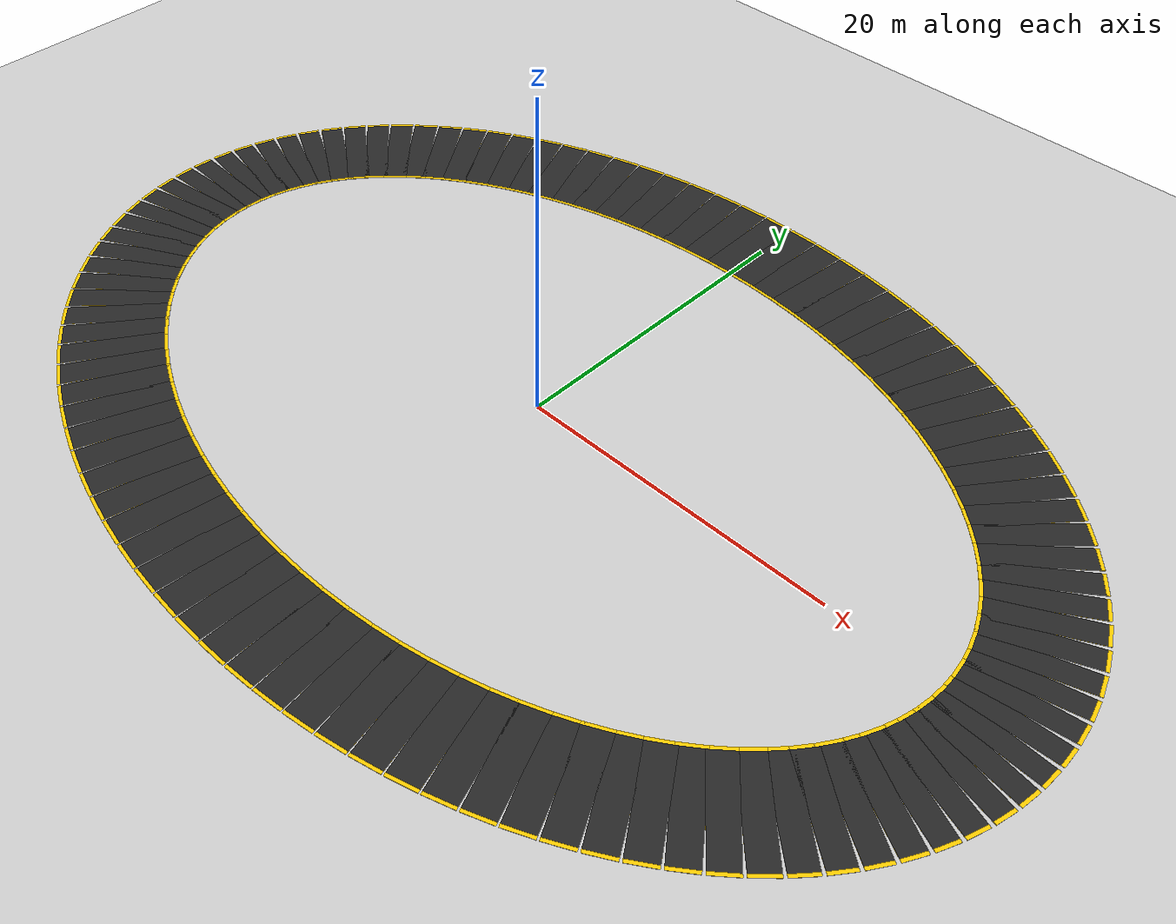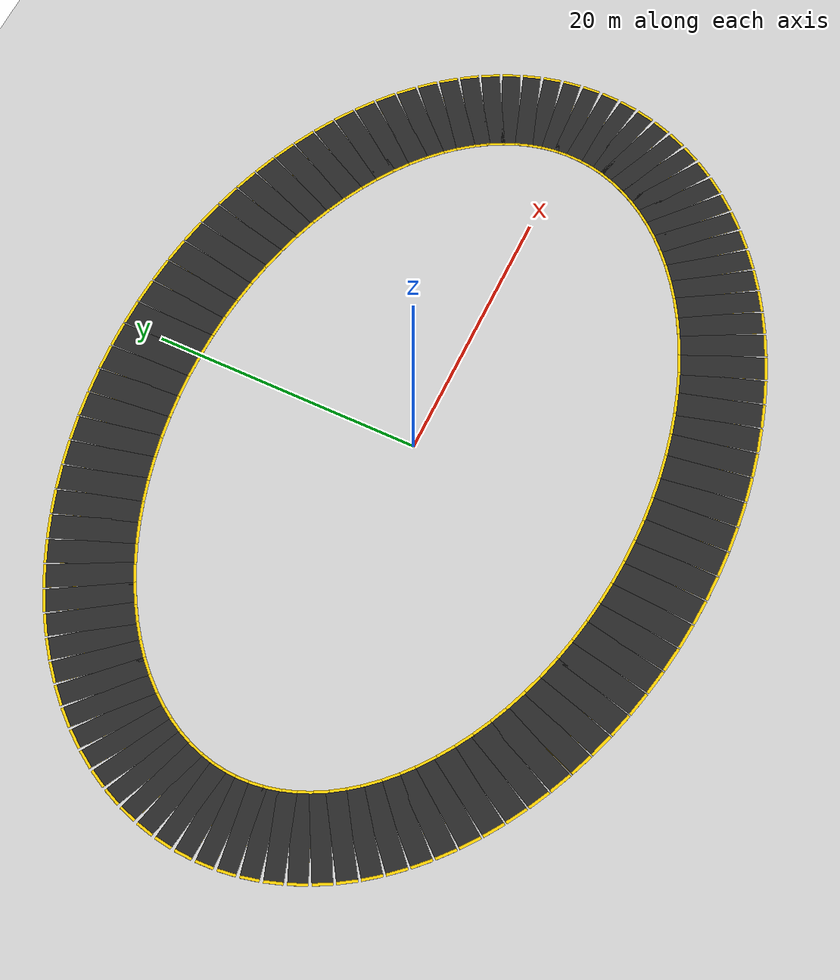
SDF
<sdf version="1.7">
 <world name="custom_road_world">
  <scene><ambient>1.0 1.0 1.0</ambient><background>0.8 0.8 0.8</background></scene>
  <plugin filename="ignition-gazebo-physics-system" name="ignition::gazebo::systems::Physics"/>
  <plugin filename="ignition-gazebo-sensors-system" name="ignition::gazebo::systems::Sensors">
   <render_engine>ogre2</render_engine>
  </plugin>
  <plugin filename="ignition-gazebo-user-commands-system" name="ignition::gazebo::systems::UserCommands"/>
  <plugin filename="ignition-gazebo-scene-broadcaster-system" name="ignition::gazebo::systems::SceneBroadcaster"/>
  <include><uri>https://fuel.ignitionrobotics.org/1.0/openrobotics/models/Ground Plane</uri></include>
  <include><uri>https://fuel.ignitionrobotics.org/1.0/openrobotics/models/Sun</uri></include>
  <model name="elliptical_road">
   <static>true</static>
   <link name="seg_0">
    <pose>29.970 0.628 0.01 0 0 1.618</pose>
    <visual name="yellow_base_0">
     <pose>0 0 0.001 0 0 0</pose>
     <geometry><box><size>1.287 6.4 0.02</size></box></geometry>
     <material>
      <ambient>1.0 0.8 0.0 1.0</ambient>
      <diffuse>1.0 0.8 0.0 1.0</diffuse>
      <specular>0.1 0.1 0.1 1.0</specular>
     </material>
    </visual>
    <visual name="asphalt_top_0">
     <pose>0 0 0.002 0 0 0</pose>
     <geometry><box><size>1.287 6.0 0.02</size></box></geometry>
     <material>
      <ambient>0.15 0.15 0.15 1.0</ambient>
      <diffuse>0.15 0.15 0.15 1.0</diffuse>
      <specular>0.05 0.05 0.05 1.0</specular>
     </material>
    </visual>
    <collision name="collision_0">
     <pose>0 0 0.002 0 0 0</pose>
     <geometry><box><size>1.287 6.0 0.02</size></box></geometry>
    </collision>
   </link>
   <link name="seg_1">
    <pose>29.852 1.881 0.01 0 0 1.712</pose>
    <visual name="yellow_base_1">
     <pose>0 0 0.001 0 0 0</pose>
     <geometry><box><size>1.293 6.4 0.02</size></box></geometry>
     <material>
      <ambient>1.0 0.8 0.0 1.0</ambient>
      <diffuse>1.0 0.8 0.0 1.0</diffuse>
      <specular>0.1 0.1 0.1 1.0</specular>
     </material>
    </visual>
    <visual name="asphalt_top_1">
     <pose>0 0 0.002 0 0 0</pose>
     <geometry><box><size>1.293 6.0 0.02</size></box></geometry>
     <material>
      <ambient>0.15 0.15 0.15 1.0</ambient>
      <diffuse>0.15 0.15 0.15 1.0</diffuse>
      <specular>0.05 0.05 0.05 1.0</specular>
     </material>
    </visual>
    <collision name="collision_1">
     <pose>0 0 0.002 0 0 0</pose>
     <geometry><box><size>1.293 6.0 0.02</size></box></geometry>
    </collision>
   </link>
   <link name="seg_2">
    <pose>29.616 3.127 0.01 0 0 1.804</pose>
    <visual name="yellow_base_2">
     <pose>0 0 0.001 0 0 0</pose>
     <geometry><box><size>1.306 6.4 0.02</size></box></geometry>
     <material>
      <ambient>1.0 0.8 0.0 1.0</ambient>
      <diffuse>1.0 0.8 0.0 1.0</diffuse>
      <specular>0.1 0.1 0.1 1.0</specular>
     </material>
    </visual>
    <visual name="asphalt_top_2">
     <pose>0 0 0.002 0 0 0</pose>
     <geometry><box><size>1.306 6.0 0.02</size></box></geometry>
     <material>
      <ambient>0.15 0.15 0.15 1.0</ambient>
      <diffuse>0.15 0.15 0.15 1.0</diffuse>
      <specular>0.05 0.05 0.05 1.0</specular>
     </material>
    </visual>
    <collision name="collision_2">
     <pose>0 0 0.002 0 0 0</pose>
     <geometry><box><size>1.306 6.0 0.02</size></box></geometry>
    </collision>
   </link>
   <link name="seg_3">
    <pose>29.263 4.361 0.01 0 0 1.894</pose>
    <visual name="yellow_base_3">
     <pose>0 0 0.001 0 0 0</pose>
     <geometry><box><size>1.323 6.4 0.02</size></box></geometry>
     <material>
      <ambient>1.0 0.8 0.0 1.0</ambient>
      <diffuse>1.0 0.8 0.0 1.0</diffuse>
      <specular>0.1 0.1 0.1 1.0</specular>
     </material>
    </visual>
    <visual name="asphalt_top_3">
     <pose>0 0 0.002 0 0 0</pose>
     <geometry><box><size>1.323 6.0 0.02</size></box></geometry>
     <material>
      <ambient>0.15 0.15 0.15 1.0</ambient>
      <diffuse>0.15 0.15 0.15 1.0</diffuse>
      <specular>0.05 0.05 0.05 1.0</specular>
     </material>
    </visual>
    <collision name="collision_3">
     <pose>0 0 0.002 0 0 0</pose>
     <geometry><box><size>1.323 6.0 0.02</size></box></geometry>
    </collision>
   </link>
   <link name="seg_4">
    <pose>28.795 5.577 0.01 0 0 1.982</pose>
    <visual name="yellow_base_4">
     <pose>0 0 0.001 0 0 0</pose>
     <geometry><box><size>1.346 6.4 0.02</size></box></geometry>
     <material>
      <ambient>1.0 0.8 0.0 1.0</ambient>
      <diffuse>1.0 0.8 0.0 1.0</diffuse>
      <specular>0.1 0.1 0.1 1.0</specular>
     </material>
    </visual>
    <visual name="asphalt_top_4">
     <pose>0 0 0.002 0 0 0</pose>
     <geometry><box><size>1.346 6.0 0.02</size></box></geometry>
     <material>
      <ambient>0.15 0.15 0.15 1.0</ambient>
      <diffuse>0.15 0.15 0.15 1.0</diffuse>
      <specular>0.05 0.05 0.05 1.0</specular>
     </material>
    </visual>
    <collision name="collision_4">
     <pose>0 0 0.002 0 0 0</pose>
     <geometry><box><size>1.346 6.0 0.02</size></box></geometry>
    </collision>
   </link>
   <link name="seg_5">
    <pose>28.212 6.771 0.01 0 0 2.066</pose>
    <visual name="yellow_base_5">
     <pose>0 0 0.001 0 0 0</pose>
     <geometry><box><size>1.374 6.4 0.02</size></box></geometry>
     <material>
      <ambient>1.0 0.8 0.0 1.0</ambient>
      <diffuse>1.0 0.8 0.0 1.0</diffuse>
      <specular>0.1 0.1 0.1 1.0</specular>
     </material>
    </visual>
    <visual name="asphalt_top_5">
     <pose>0 0 0.002 0 0 0</pose>
     <geometry><box><size>1.374 6.0 0.02</size></box></geometry>
     <material>
      <ambient>0.15 0.15 0.15 1.0</ambient>
      <diffuse>0.15 0.15 0.15 1.0</diffuse>
      <specular>0.05 0.05 0.05 1.0</specular>
     </material>
    </visual>
    <collision name="collision_5">
     <pose>0 0 0.002 0 0 0</pose>
     <geometry><box><size>1.374 6.0 0.02</size></box></geometry>
    </collision>
   </link>
   <link name="seg_6">
    <pose>27.519 7.939 0.01 0 0 2.147</pose>
    <visual name="yellow_base_6">
     <pose>0 0 0.001 0 0 0</pose>
     <geometry><box><size>1.405 6.4 0.02</size></box></geometry>
     <material>
      <ambient>1.0 0.8 0.0 1.0</ambient>
      <diffuse>1.0 0.8 0.0 1.0</diffuse>
      <specular>0.1 0.1 0.1 1.0</specular>
     </material>
    </visual>
    <visual name="asphalt_top_6">
     <pose>0 0 0.002 0 0 0</pose>
     <geometry><box><size>1.405 6.0 0.02</size></box></geometry>
     <material>
      <ambient>0.15 0.15 0.15 1.0</ambient>
      <diffuse>0.15 0.15 0.15 1.0</diffuse>
      <specular>0.05 0.05 0.05 1.0</specular>
     </material>
    </visual>
    <collision name="collision_6">
     <pose>0 0 0.002 0 0 0</pose>
     <geometry><box><size>1.405 6.0 0.02</size></box></geometry>
    </collision>
   </link>
   <link name="seg_7">
    <pose>26.717 9.075 0.01 0 0 2.223</pose>
    <visual name="yellow_base_7">
     <pose>0 0 0.001 0 0 0</pose>
     <geometry><box><size>1.439 6.4 0.02</size></box></geometry>
     <material>
      <ambient>1.0 0.8 0.0 1.0</ambient>
      <diffuse>1.0 0.8 0.0 1.0</diffuse>
      <specular>0.1 0.1 0.1 1.0</specular>
     </material>
    </visual>
    <visual name="asphalt_top_7">
     <pose>0 0 0.002 0 0 0</pose>
     <geometry><box><size>1.439 6.0 0.02</size></box></geometry>
     <material>
      <ambient>0.15 0.15 0.15 1.0</ambient>
      <diffuse>0.15 0.15 0.15 1.0</diffuse>
      <specular>0.05 0.05 0.05 1.0</specular>
     </material>
    </visual>
    <collision name="collision_7">
     <pose>0 0 0.002 0 0 0</pose>
     <geometry><box><size>1.439 6.0 0.02</size></box></geometry>
    </collision>
   </link>
   <link name="seg_8">
    <pose>25.810 10.176 0.01 0 0 2.296</pose>
    <visual name="yellow_base_8">
     <pose>0 0 0.001 0 0 0</pose>
     <geometry><box><size>1.476 6.4 0.02</size></box></geometry>
     <material>
      <ambient>1.0 0.8 0.0 1.0</ambient>
      <diffuse>1.0 0.8 0.0 1.0</diffuse>
      <specular>0.1 0.1 0.1 1.0</specular>
     </material>
    </visual>
    <visual name="asphalt_top_8">
     <pose>0 0 0.002 0 0 0</pose>
     <geometry><box><size>1.476 6.0 0.02</size></box></geometry>
     <material>
      <ambient>0.15 0.15 0.15 1.0</ambient>
      <diffuse>0.15 0.15 0.15 1.0</diffuse>
      <specular>0.05 0.05 0.05 1.0</specular>
     </material>
    </visual>
    <collision name="collision_8">
     <pose>0 0 0.002 0 0 0</pose>
     <geometry><box><size>1.476 6.0 0.02</size></box></geometry>
    </collision>
   </link>
   <link name="seg_9">
    <pose>24.800 11.236 0.01 0 0 2.366</pose>
    <visual name="yellow_base_9">
     <pose>0 0 0.001 0 0 0</pose>
     <geometry><box><size>1.514 6.4 0.02</size></box></geometry>
     <material>
      <ambient>1.0 0.8 0.0 1.0</ambient>
      <diffuse>1.0 0.8 0.0 1.0</diffuse>
      <specular>0.1 0.1 0.1 1.0</specular>
     </material>
    </visual>
    <visual name="asphalt_top_9">
     <pose>0 0 0.002 0 0 0</pose>
     <geometry><box><size>1.514 6.0 0.02</size></box></geometry>
     <material>
      <ambient>0.15 0.15 0.15 1.0</ambient>
      <diffuse>0.15 0.15 0.15 1.0</diffuse>
      <specular>0.05 0.05 0.05 1.0</specular>
     </material>
    </visual>
    <collision name="collision_9">
     <pose>0 0 0.002 0 0 0</pose>
     <geometry><box><size>1.514 6.0 0.02</size></box></geometry>
    </collision>
   </link>
   <link name="seg_10">
    <pose>23.693 12.252 0.01 0 0 2.432</pose>
    <visual name="yellow_base_10">
     <pose>0 0 0.001 0 0 0</pose>
     <geometry><box><size>1.553 6.4 0.02</size></box></geometry>
     <material>
      <ambient>1.0 0.8 0.0 1.0</ambient>
      <diffuse>1.0 0.8 0.0 1.0</diffuse>
      <specular>0.1 0.1 0.1 1.0</specular>
     </material>
    </visual>
    <visual name="asphalt_top_10">
     <pose>0 0 0.002 0 0 0</pose>
     <geometry><box><size>1.553 6.0 0.02</size></box></geometry>
     <material>
      <ambient>0.15 0.15 0.15 1.0</ambient>
      <diffuse>0.15 0.15 0.15 1.0</diffuse>
      <specular>0.05 0.05 0.05 1.0</specular>
     </material>
    </visual>
    <collision name="collision_10">
     <pose>0 0 0.002 0 0 0</pose>
     <geometry><box><size>1.553 6.0 0.02</size></box></geometry>
    </collision>
   </link>
   <link name="seg_11">
    <pose>22.492 13.220 0.01 0 0 2.494</pose>
    <visual name="yellow_base_11">
     <pose>0 0 0.001 0 0 0</pose>
     <geometry><box><size>1.593 6.4 0.02</size></box></geometry>
     <material>
      <ambient>1.0 0.8 0.0 1.0</ambient>
      <diffuse>1.0 0.8 0.0 1.0</diffuse>
      <specular>0.1 0.1 0.1 1.0</specular>
     </material>
    </visual>
    <visual name="asphalt_top_11">
     <pose>0 0 0.002 0 0 0</pose>
     <geometry><box><size>1.593 6.0 0.02</size></box></geometry>
     <material>
      <ambient>0.15 0.15 0.15 1.0</ambient>
      <diffuse>0.15 0.15 0.15 1.0</diffuse>
      <specular>0.05 0.05 0.05 1.0</specular>
     </material>
    </visual>
    <collision name="collision_11">
     <pose>0 0 0.002 0 0 0</pose>
     <geometry><box><size>1.593 6.0 0.02</size></box></geometry>
    </collision>
   </link>
   <link name="seg_12">
    <pose>21.203 14.135 0.01 0 0 2.554</pose>
    <visual name="yellow_base_12">
     <pose>0 0 0.001 0 0 0</pose>
     <geometry><box><size>1.632 6.4 0.02</size></box></geometry>
     <material>
      <ambient>1.0 0.8 0.0 1.0</ambient>
      <diffuse>1.0 0.8 0.0 1.0</diffuse>
      <specular>0.1 0.1 0.1 1.0</specular>
     </material>
    </visual>
    <visual name="asphalt_top_12">
     <pose>0 0 0.002 0 0 0</pose>
     <geometry><box><size>1.632 6.0 0.02</size></box></geometry>
     <material>
      <ambient>0.15 0.15 0.15 1.0</ambient>
      <diffuse>0.15 0.15 0.15 1.0</diffuse>
      <specular>0.05 0.05 0.05 1.0</specular>
     </material>
    </visual>
    <collision name="collision_12">
     <pose>0 0 0.002 0 0 0</pose>
     <geometry><box><size>1.632 6.0 0.02</size></box></geometry>
    </collision>
   </link>
   <link name="seg_13">
    <pose>19.830 14.995 0.01 0 0 2.610</pose>
    <visual name="yellow_base_13">
     <pose>0 0 0.001 0 0 0</pose>
     <geometry><box><size>1.670 6.4 0.02</size></box></geometry>
     <material>
      <ambient>1.0 0.8 0.0 1.0</ambient>
      <diffuse>1.0 0.8 0.0 1.0</diffuse>
      <specular>0.1 0.1 0.1 1.0</specular>
     </material>
    </visual>
    <visual name="asphalt_top_13">
     <pose>0 0 0.002 0 0 0</pose>
     <geometry><box><size>1.670 6.0 0.02</size></box></geometry>
     <material>
      <ambient>0.15 0.15 0.15 1.0</ambient>
      <diffuse>0.15 0.15 0.15 1.0</diffuse>
      <specular>0.05 0.05 0.05 1.0</specular>
     </material>
    </visual>
    <collision name="collision_13">
     <pose>0 0 0.002 0 0 0</pose>
     <geometry><box><size>1.670 6.0 0.02</size></box></geometry>
    </collision>
   </link>
   <link name="seg_14">
    <pose>18.378 15.795 0.01 0 0 2.664</pose>
    <visual name="yellow_base_14">
     <pose>0 0 0.001 0 0 0</pose>
     <geometry><box><size>1.706 6.4 0.02</size></box></geometry>
     <material>
      <ambient>1.0 0.8 0.0 1.0</ambient>
      <diffuse>1.0 0.8 0.0 1.0</diffuse>
      <specular>0.1 0.1 0.1 1.0</specular>
     </material>
    </visual>
    <visual name="asphalt_top_14">
     <pose>0 0 0.002 0 0 0</pose>
     <geometry><box><size>1.706 6.0 0.02</size></box></geometry>
     <material>
      <ambient>0.15 0.15 0.15 1.0</ambient>
      <diffuse>0.15 0.15 0.15 1.0</diffuse>
      <specular>0.05 0.05 0.05 1.0</specular>
     </material>
    </visual>
    <collision name="collision_14">
     <pose>0 0 0.002 0 0 0</pose>
     <geometry><box><size>1.706 6.0 0.02</size></box></geometry>
    </collision>
   </link>
   <link name="seg_15">
    <pose>16.854 16.533 0.01 0 0 2.716</pose>
    <visual name="yellow_base_15">
     <pose>0 0 0.001 0 0 0</pose>
     <geometry><box><size>1.741 6.4 0.02</size></box></geometry>
     <material>
      <ambient>1.0 0.8 0.0 1.0</ambient>
      <diffuse>1.0 0.8 0.0 1.0</diffuse>
      <specular>0.1 0.1 0.1 1.0</specular>
     </material>
    </visual>
    <visual name="asphalt_top_15">
     <pose>0 0 0.002 0 0 0</pose>
     <geometry><box><size>1.741 6.0 0.02</size></box></geometry>
     <material>
      <ambient>0.15 0.15 0.15 1.0</ambient>
      <diffuse>0.15 0.15 0.15 1.0</diffuse>
      <specular>0.05 0.05 0.05 1.0</specular>
     </material>
    </visual>
    <collision name="collision_15">
     <pose>0 0 0.002 0 0 0</pose>
     <geometry><box><size>1.741 6.0 0.02</size></box></geometry>
    </collision>
   </link>
   <link name="seg_16">
    <pose>15.264 17.206 0.01 0 0 2.766</pose>
    <visual name="yellow_base_16">
     <pose>0 0 0.001 0 0 0</pose>
     <geometry><box><size>1.774 6.4 0.02</size></box></geometry>
     <material>
      <ambient>1.0 0.8 0.0 1.0</ambient>
      <diffuse>1.0 0.8 0.0 1.0</diffuse>
      <specular>0.1 0.1 0.1 1.0</specular>
     </material>
    </visual>
    <visual name="asphalt_top_16">
     <pose>0 0 0.002 0 0 0</pose>
     <geometry><box><size>1.774 6.0 0.02</size></box></geometry>
     <material>
      <ambient>0.15 0.15 0.15 1.0</ambient>
      <diffuse>0.15 0.15 0.15 1.0</diffuse>
      <specular>0.05 0.05 0.05 1.0</specular>
     </material>
    </visual>
    <collision name="collision_16">
     <pose>0 0 0.002 0 0 0</pose>
     <geometry><box><size>1.774 6.0 0.02</size></box></geometry>
    </collision>
   </link>
   <link name="seg_17">
    <pose>13.613 17.811 0.01 0 0 2.814</pose>
    <visual name="yellow_base_17">
     <pose>0 0 0.001 0 0 0</pose>
     <geometry><box><size>1.803 6.4 0.02</size></box></geometry>
     <material>
      <ambient>1.0 0.8 0.0 1.0</ambient>
      <diffuse>1.0 0.8 0.0 1.0</diffuse>
      <specular>0.1 0.1 0.1 1.0</specular>
     </material>
    </visual>
    <visual name="asphalt_top_17">
     <pose>0 0 0.002 0 0 0</pose>
     <geometry><box><size>1.803 6.0 0.02</size></box></geometry>
     <material>
      <ambient>0.15 0.15 0.15 1.0</ambient>
      <diffuse>0.15 0.15 0.15 1.0</diffuse>
      <specular>0.05 0.05 0.05 1.0</specular>
     </material>
    </visual>
    <collision name="collision_17">
     <pose>0 0 0.002 0 0 0</pose>
     <geometry><box><size>1.803 6.0 0.02</size></box></geometry>
    </collision>
   </link>
   <link name="seg_18">
    <pose>11.909 18.346 0.01 0 0 2.861</pose>
    <visual name="yellow_base_18">
     <pose>0 0 0.001 0 0 0</pose>
     <geometry><box><size>1.830 6.4 0.02</size></box></geometry>
     <material>
      <ambient>1.0 0.8 0.0 1.0</ambient>
      <diffuse>1.0 0.8 0.0 1.0</diffuse>
      <specular>0.1 0.1 0.1 1.0</specular>
     </material>
    </visual>
    <visual name="asphalt_top_18">
     <pose>0 0 0.002 0 0 0</pose>
     <geometry><box><size>1.830 6.0 0.02</size></box></geometry>
     <material>
      <ambient>0.15 0.15 0.15 1.0</ambient>
      <diffuse>0.15 0.15 0.15 1.0</diffuse>
      <specular>0.05 0.05 0.05 1.0</specular>
     </material>
    </visual>
    <collision name="collision_18">
     <pose>0 0 0.002 0 0 0</pose>
     <geometry><box><size>1.830 6.0 0.02</size></box></geometry>
    </collision>
   </link>
   <link name="seg_19">
    <pose>10.157 18.808 0.01 0 0 2.906</pose>
    <visual name="yellow_base_19">
     <pose>0 0 0.001 0 0 0</pose>
     <geometry><box><size>1.854 6.4 0.02</size></box></geometry>
     <material>
      <ambient>1.0 0.8 0.0 1.0</ambient>
      <diffuse>1.0 0.8 0.0 1.0</diffuse>
      <specular>0.1 0.1 0.1 1.0</specular>
     </material>
    </visual>
    <visual name="asphalt_top_19">
     <pose>0 0 0.002 0 0 0</pose>
     <geometry><box><size>1.854 6.0 0.02</size></box></geometry>
     <material>
      <ambient>0.15 0.15 0.15 1.0</ambient>
      <diffuse>0.15 0.15 0.15 1.0</diffuse>
      <specular>0.05 0.05 0.05 1.0</specular>
     </material>
    </visual>
    <collision name="collision_19">
     <pose>0 0 0.002 0 0 0</pose>
     <geometry><box><size>1.854 6.0 0.02</size></box></geometry>
    </collision>
   </link>
   <link name="seg_20">
    <pose>8.366 19.196 0.01 0 0 2.950</pose>
    <visual name="yellow_base_20">
     <pose>0 0 0.001 0 0 0</pose>
     <geometry><box><size>1.873 6.4 0.02</size></box></geometry>
     <material>
      <ambient>1.0 0.8 0.0 1.0</ambient>
      <diffuse>1.0 0.8 0.0 1.0</diffuse>
      <specular>0.1 0.1 0.1 1.0</specular>
     </material>
    </visual>
    <visual name="asphalt_top_20">
     <pose>0 0 0.002 0 0 0</pose>
     <geometry><box><size>1.873 6.0 0.02</size></box></geometry>
     <material>
      <ambient>0.15 0.15 0.15 1.0</ambient>
      <diffuse>0.15 0.15 0.15 1.0</diffuse>
      <specular>0.05 0.05 0.05 1.0</specular>
     </material>
    </visual>
    <collision name="collision_20">
     <pose>0 0 0.002 0 0 0</pose>
     <geometry><box><size>1.873 6.0 0.02</size></box></geometry>
    </collision>
   </link>
   <link name="seg_21">
    <pose>6.541 19.509 0.01 0 0 2.994</pose>
    <visual name="yellow_base_21">
     <pose>0 0 0.001 0 0 0</pose>
     <geometry><box><size>1.890 6.4 0.02</size></box></geometry>
     <material>
      <ambient>1.0 0.8 0.0 1.0</ambient>
      <diffuse>1.0 0.8 0.0 1.0</diffuse>
      <specular>0.1 0.1 0.1 1.0</specular>
     </material>
    </visual>
    <visual name="asphalt_top_21">
     <pose>0 0 0.002 0 0 0</pose>
     <geometry><box><size>1.890 6.0 0.02</size></box></geometry>
     <material>
      <ambient>0.15 0.15 0.15 1.0</ambient>
      <diffuse>0.15 0.15 0.15 1.0</diffuse>
      <specular>0.05 0.05 0.05 1.0</specular>
     </material>
    </visual>
    <collision name="collision_21">
     <pose>0 0 0.002 0 0 0</pose>
     <geometry><box><size>1.890 6.0 0.02</size></box></geometry>
    </collision>
   </link>
   <link name="seg_22">
    <pose>4.691 19.744 0.01 0 0 3.036</pose>
    <visual name="yellow_base_22">
     <pose>0 0 0.001 0 0 0</pose>
     <geometry><box><size>1.902 6.4 0.02</size></box></geometry>
     <material>
      <ambient>1.0 0.8 0.0 1.0</ambient>
      <diffuse>1.0 0.8 0.0 1.0</diffuse>
      <specular>0.1 0.1 0.1 1.0</specular>
     </material>
    </visual>
    <visual name="asphalt_top_22">
     <pose>0 0 0.002 0 0 0</pose>
     <geometry><box><size>1.902 6.0 0.02</size></box></geometry>
     <material>
      <ambient>0.15 0.15 0.15 1.0</ambient>
      <diffuse>0.15 0.15 0.15 1.0</diffuse>
      <specular>0.05 0.05 0.05 1.0</specular>
     </material>
    </visual>
    <collision name="collision_22">
     <pose>0 0 0.002 0 0 0</pose>
     <geometry><box><size>1.902 6.0 0.02</size></box></geometry>
    </collision>
   </link>
   <link name="seg_23">
    <pose>2.822 19.901 0.01 0 0 3.079</pose>
    <visual name="yellow_base_23">
     <pose>0 0 0.001 0 0 0</pose>
     <geometry><box><size>1.910 6.4 0.02</size></box></geometry>
     <material>
      <ambient>1.0 0.8 0.0 1.0</ambient>
      <diffuse>1.0 0.8 0.0 1.0</diffuse>
      <specular>0.1 0.1 0.1 1.0</specular>
     </material>
    </visual>
    <visual name="asphalt_top_23">
     <pose>0 0 0.002 0 0 0</pose>
     <geometry><box><size>1.910 6.0 0.02</size></box></geometry>
     <material>
      <ambient>0.15 0.15 0.15 1.0</ambient>
      <diffuse>0.15 0.15 0.15 1.0</diffuse>
      <specular>0.05 0.05 0.05 1.0</specular>
     </material>
    </visual>
    <collision name="collision_23">
     <pose>0 0 0.002 0 0 0</pose>
     <geometry><box><size>1.910 6.0 0.02</size></box></geometry>
    </collision>
   </link>
   <link name="seg_24">
    <pose>0.942 19.980 0.01 0 0 3.121</pose>
    <visual name="yellow_base_24">
     <pose>0 0 0.001 0 0 0</pose>
     <geometry><box><size>1.914 6.4 0.02</size></box></geometry>
     <material>
      <ambient>1.0 0.8 0.0 1.0</ambient>
      <diffuse>1.0 0.8 0.0 1.0</diffuse>
      <specular>0.1 0.1 0.1 1.0</specular>
     </material>
    </visual>
    <visual name="asphalt_top_24">
     <pose>0 0 0.002 0 0 0</pose>
     <geometry><box><size>1.914 6.0 0.02</size></box></geometry>
     <material>
      <ambient>0.15 0.15 0.15 1.0</ambient>
      <diffuse>0.15 0.15 0.15 1.0</diffuse>
      <specular>0.05 0.05 0.05 1.0</specular>
     </material>
    </visual>
    <collision name="collision_24">
     <pose>0 0 0.002 0 0 0</pose>
     <geometry><box><size>1.914 6.0 0.02</size></box></geometry>
    </collision>
   </link>
   <link name="seg_25">
    <pose>-0.942 19.980 0.01 0 0 -3.121</pose>
    <visual name="yellow_base_25">
     <pose>0 0 0.001 0 0 0</pose>
     <geometry><box><size>1.914 6.4 0.02</size></box></geometry>
     <material>
      <ambient>1.0 0.8 0.0 1.0</ambient>
      <diffuse>1.0 0.8 0.0 1.0</diffuse>
      <specular>0.1 0.1 0.1 1.0</specular>
     </material>
    </visual>
    <visual name="asphalt_top_25">
     <pose>0 0 0.002 0 0 0</pose>
     <geometry><box><size>1.914 6.0 0.02</size></box></geometry>
     <material>
      <ambient>0.15 0.15 0.15 1.0</ambient>
      <diffuse>0.15 0.15 0.15 1.0</diffuse>
      <specular>0.05 0.05 0.05 1.0</specular>
     </material>
    </visual>
    <collision name="collision_25">
     <pose>0 0 0.002 0 0 0</pose>
     <geometry><box><size>1.914 6.0 0.02</size></box></geometry>
    </collision>
   </link>
   <link name="seg_26">
    <pose>-2.822 19.901 0.01 0 0 -3.079</pose>
    <visual name="yellow_base_26">
     <pose>0 0 0.001 0 0 0</pose>
     <geometry><box><size>1.910 6.4 0.02</size></box></geometry>
     <material>
      <ambient>1.0 0.8 0.0 1.0</ambient>
      <diffuse>1.0 0.8 0.0 1.0</diffuse>
      <specular>0.1 0.1 0.1 1.0</specular>
     </material>
    </visual>
    <visual name="asphalt_top_26">
     <pose>0 0 0.002 0 0 0</pose>
     <geometry><box><size>1.910 6.0 0.02</size></box></geometry>
     <material>
      <ambient>0.15 0.15 0.15 1.0</ambient>
      <diffuse>0.15 0.15 0.15 1.0</diffuse>
      <specular>0.05 0.05 0.05 1.0</specular>
     </material>
    </visual>
    <collision name="collision_26">
     <pose>0 0 0.002 0 0 0</pose>
     <geometry><box><size>1.910 6.0 0.02</size></box></geometry>
    </collision>
   </link>
   <link name="seg_27">
    <pose>-4.691 19.744 0.01 0 0 -3.036</pose>
    <visual name="yellow_base_27">
     <pose>0 0 0.001 0 0 0</pose>
     <geometry><box><size>1.902 6.4 0.02</size></box></geometry>
     <material>
      <ambient>1.0 0.8 0.0 1.0</ambient>
      <diffuse>1.0 0.8 0.0 1.0</diffuse>
      <specular>0.1 0.1 0.1 1.0</specular>
     </material>
    </visual>
    <visual name="asphalt_top_27">
     <pose>0 0 0.002 0 0 0</pose>
     <geometry><box><size>1.902 6.0 0.02</size></box></geometry>
     <material>
      <ambient>0.15 0.15 0.15 1.0</ambient>
      <diffuse>0.15 0.15 0.15 1.0</diffuse>
      <specular>0.05 0.05 0.05 1.0</specular>
     </material>
    </visual>
    <collision name="collision_27">
     <pose>0 0 0.002 0 0 0</pose>
     <geometry><box><size>1.902 6.0 0.02</size></box></geometry>
    </collision>
   </link>
   <link name="seg_28">
    <pose>-6.541 19.509 0.01 0 0 -2.994</pose>
    <visual name="yellow_base_28">
     <pose>0 0 0.001 0 0 0</pose>
     <geometry><box><size>1.890 6.4 0.02</size></box></geometry>
     <material>
      <ambient>1.0 0.8 0.0 1.0</ambient>
      <diffuse>1.0 0.8 0.0 1.0</diffuse>
      <specular>0.1 0.1 0.1 1.0</specular>
     </material>
    </visual>
    <visual name="asphalt_top_28">
     <pose>0 0 0.002 0 0 0</pose>
     <geometry><box><size>1.890 6.0 0.02</size></box></geometry>
     <material>
      <ambient>0.15 0.15 0.15 1.0</ambient>
      <diffuse>0.15 0.15 0.15 1.0</diffuse>
      <specular>0.05 0.05 0.05 1.0</specular>
     </material>
    </visual>
    <collision name="collision_28">
     <pose>0 0 0.002 0 0 0</pose>
     <geometry><box><size>1.890 6.0 0.02</size></box></geometry>
    </collision>
   </link>
   <link name="seg_29">
    <pose>-8.366 19.196 0.01 0 0 -2.950</pose>
    <visual name="yellow_base_29">
     <pose>0 0 0.001 0 0 0</pose>
     <geometry><box><size>1.873 6.4 0.02</size></box></geometry>
     <material>
      <ambient>1.0 0.8 0.0 1.0</ambient>
      <diffuse>1.0 0.8 0.0 1.0</diffuse>
      <specular>0.1 0.1 0.1 1.0</specular>
     </material>
    </visual>
    <visual name="asphalt_top_29">
     <pose>0 0 0.002 0 0 0</pose>
     <geometry><box><size>1.873 6.0 0.02</size></box></geometry>
     <material>
      <ambient>0.15 0.15 0.15 1.0</ambient>
      <diffuse>0.15 0.15 0.15 1.0</diffuse>
      <specular>0.05 0.05 0.05 1.0</specular>
     </material>
    </visual>
    <collision name="collision_29">
     <pose>0 0 0.002 0 0 0</pose>
     <geometry><box><size>1.873 6.0 0.02</size></box></geometry>
    </collision>
   </link>
   <link name="seg_30">
    <pose>-10.157 18.808 0.01 0 0 -2.906</pose>
    <visual name="yellow_base_30">
     <pose>0 0 0.001 0 0 0</pose>
     <geometry><box><size>1.854 6.4 0.02</size></box></geometry>
     <material>
      <ambient>1.0 0.8 0.0 1.0</ambient>
      <diffuse>1.0 0.8 0.0 1.0</diffuse>
      <specular>0.1 0.1 0.1 1.0</specular>
     </material>
    </visual>
    <visual name="asphalt_top_30">
     <pose>0 0 0.002 0 0 0</pose>
     <geometry><box><size>1.854 6.0 0.02</size></box></geometry>
     <material>
      <ambient>0.15 0.15 0.15 1.0</ambient>
      <diffuse>0.15 0.15 0.15 1.0</diffuse>
      <specular>0.05 0.05 0.05 1.0</specular>
     </material>
    </visual>
    <collision name="collision_30">
     <pose>0 0 0.002 0 0 0</pose>
     <geometry><box><size>1.854 6.0 0.02</size></box></geometry>
    </collision>
   </link>
   <link name="seg_31">
    <pose>-11.909 18.346 0.01 0 0 -2.861</pose>
    <visual name="yellow_base_31">
     <pose>0 0 0.001 0 0 0</pose>
     <geometry><box><size>1.830 6.4 0.02</size></box></geometry>
     <material>
      <ambient>1.0 0.8 0.0 1.0</ambient>
      <diffuse>1.0 0.8 0.0 1.0</diffuse>
      <specular>0.1 0.1 0.1 1.0</specular>
     </material>
    </visual>
    <visual name="asphalt_top_31">
     <pose>0 0 0.002 0 0 0</pose>
     <geometry><box><size>1.830 6.0 0.02</size></box></geometry>
     <material>
      <ambient>0.15 0.15 0.15 1.0</ambient>
      <diffuse>0.15 0.15 0.15 1.0</diffuse>
      <specular>0.05 0.05 0.05 1.0</specular>
     </material>
    </visual>
    <collision name="collision_31">
     <pose>0 0 0.002 0 0 0</pose>
     <geometry><box><size>1.830 6.0 0.02</size></box></geometry>
    </collision>
   </link>
   <link name="seg_32">
    <pose>-13.613 17.811 0.01 0 0 -2.814</pose>
    <visual name="yellow_base_32">
     <pose>0 0 0.001 0 0 0</pose>
     <geometry><box><size>1.803 6.4 0.02</size></box></geometry>
     <material>
      <ambient>1.0 0.8 0.0 1.0</ambient>
      <diffuse>1.0 0.8 0.0 1.0</diffuse>
      <specular>0.1 0.1 0.1 1.0</specular>
     </material>
    </visual>
    <visual name="asphalt_top_32">
     <pose>0 0 0.002 0 0 0</pose>
     <geometry><box><size>1.803 6.0 0.02</size></box></geometry>
     <material>
      <ambient>0.15 0.15 0.15 1.0</ambient>
      <diffuse>0.15 0.15 0.15 1.0</diffuse>
      <specular>0.05 0.05 0.05 1.0</specular>
     </material>
    </visual>
    <collision name="collision_32">
     <pose>0 0 0.002 0 0 0</pose>
     <geometry><box><size>1.803 6.0 0.02</size></box></geometry>
    </collision>
   </link>
   <link name="seg_33">
    <pose>-15.264 17.206 0.01 0 0 -2.766</pose>
    <visual name="yellow_base_33">
     <pose>0 0 0.001 0 0 0</pose>
     <geometry><box><size>1.774 6.4 0.02</size></box></geometry>
     <material>
      <ambient>1.0 0.8 0.0 1.0</ambient>
      <diffuse>1.0 0.8 0.0 1.0</diffuse>
      <specular>0.1 0.1 0.1 1.0</specular>
     </material>
    </visual>
    <visual name="asphalt_top_33">
     <pose>0 0 0.002 0 0 0</pose>
     <geometry><box><size>1.774 6.0 0.02</size></box></geometry>
     <material>
      <ambient>0.15 0.15 0.15 1.0</ambient>
      <diffuse>0.15 0.15 0.15 1.0</diffuse>
      <specular>0.05 0.05 0.05 1.0</specular>
     </material>
    </visual>
    <collision name="collision_33">
     <pose>0 0 0.002 0 0 0</pose>
     <geometry><box><size>1.774 6.0 0.02</size></box></geometry>
    </collision>
   </link>
   <link name="seg_34">
    <pose>-16.854 16.533 0.01 0 0 -2.716</pose>
    <visual name="yellow_base_34">
     <pose>0 0 0.001 0 0 0</pose>
     <geometry><box><size>1.741 6.4 0.02</size></box></geometry>
     <material>
      <ambient>1.0 0.8 0.0 1.0</ambient>
      <diffuse>1.0 0.8 0.0 1.0</diffuse>
      <specular>0.1 0.1 0.1 1.0</specular>
     </material>
    </visual>
    <visual name="asphalt_top_34">
     <pose>0 0 0.002 0 0 0</pose>
     <geometry><box><size>1.741 6.0 0.02</size></box></geometry>
     <material>
      <ambient>0.15 0.15 0.15 1.0</ambient>
      <diffuse>0.15 0.15 0.15 1.0</diffuse>
      <specular>0.05 0.05 0.05 1.0</specular>
     </material>
    </visual>
    <collision name="collision_34">
     <pose>0 0 0.002 0 0 0</pose>
     <geometry><box><size>1.741 6.0 0.02</size></box></geometry>
    </collision>
   </link>
   <link name="seg_35">
    <pose>-18.378 15.795 0.01 0 0 -2.664</pose>
    <visual name="yellow_base_35">
     <pose>0 0 0.001 0 0 0</pose>
     <geometry><box><size>1.706 6.4 0.02</size></box></geometry>
     <material>
      <ambient>1.0 0.8 0.0 1.0</ambient>
      <diffuse>1.0 0.8 0.0 1.0</diffuse>
      <specular>0.1 0.1 0.1 1.0</specular>
     </material>
    </visual>
    <visual name="asphalt_top_35">
     <pose>0 0 0.002 0 0 0</pose>
     <geometry><box><size>1.706 6.0 0.02</size></box></geometry>
     <material>
      <ambient>0.15 0.15 0.15 1.0</ambient>
      <diffuse>0.15 0.15 0.15 1.0</diffuse>
      <specular>0.05 0.05 0.05 1.0</specular>
     </material>
    </visual>
    <collision name="collision_35">
     <pose>0 0 0.002 0 0 0</pose>
     <geometry><box><size>1.706 6.0 0.02</size></box></geometry>
    </collision>
   </link>
   <link name="seg_36">
    <pose>-19.830 14.995 0.01 0 0 -2.610</pose>
    <visual name="yellow_base_36">
     <pose>0 0 0.001 0 0 0</pose>
     <geometry><box><size>1.670 6.4 0.02</size></box></geometry>
     <material>
      <ambient>1.0 0.8 0.0 1.0</ambient>
      <diffuse>1.0 0.8 0.0 1.0</diffuse>
      <specular>0.1 0.1 0.1 1.0</specular>
     </material>
    </visual>
    <visual name="asphalt_top_36">
     <pose>0 0 0.002 0 0 0</pose>
     <geometry><box><size>1.670 6.0 0.02</size></box></geometry>
     <material>
      <ambient>0.15 0.15 0.15 1.0</ambient>
      <diffuse>0.15 0.15 0.15 1.0</diffuse>
      <specular>0.05 0.05 0.05 1.0</specular>
     </material>
    </visual>
    <collision name="collision_36">
     <pose>0 0 0.002 0 0 0</pose>
     <geometry><box><size>1.670 6.0 0.02</size></box></geometry>
    </collision>
   </link>
   <link name="seg_37">
    <pose>-21.203 14.135 0.01 0 0 -2.554</pose>
    <visual name="yellow_base_37">
     <pose>0 0 0.001 0 0 0</pose>
     <geometry><box><size>1.632 6.4 0.02</size></box></geometry>
     <material>
      <ambient>1.0 0.8 0.0 1.0</ambient>
      <diffuse>1.0 0.8 0.0 1.0</diffuse>
      <specular>0.1 0.1 0.1 1.0</specular>
     </material>
    </visual>
    <visual name="asphalt_top_37">
     <pose>0 0 0.002 0 0 0</pose>
     <geometry><box><size>1.632 6.0 0.02</size></box></geometry>
     <material>
      <ambient>0.15 0.15 0.15 1.0</ambient>
      <diffuse>0.15 0.15 0.15 1.0</diffuse>
      <specular>0.05 0.05 0.05 1.0</specular>
     </material>
    </visual>
    <collision name="collision_37">
     <pose>0 0 0.002 0 0 0</pose>
     <geometry><box><size>1.632 6.0 0.02</size></box></geometry>
    </collision>
   </link>
   <link name="seg_38">
    <pose>-22.492 13.220 0.01 0 0 -2.494</pose>
    <visual name="yellow_base_38">
     <pose>0 0 0.001 0 0 0</pose>
     <geometry><box><size>1.593 6.4 0.02</size></box></geometry>
     <material>
      <ambient>1.0 0.8 0.0 1.0</ambient>
      <diffuse>1.0 0.8 0.0 1.0</diffuse>
      <specular>0.1 0.1 0.1 1.0</specular>
     </material>
    </visual>
    <visual name="asphalt_top_38">
     <pose>0 0 0.002 0 0 0</pose>
     <geometry><box><size>1.593 6.0 0.02</size></box></geometry>
     <material>
      <ambient>0.15 0.15 0.15 1.0</ambient>
      <diffuse>0.15 0.15 0.15 1.0</diffuse>
      <specular>0.05 0.05 0.05 1.0</specular>
     </material>
    </visual>
    <collision name="collision_38">
     <pose>0 0 0.002 0 0 0</pose>
     <geometry><box><size>1.593 6.0 0.02</size></box></geometry>
    </collision>
   </link>
   <link name="seg_39">
    <pose>-23.693 12.252 0.01 0 0 -2.432</pose>
    <visual name="yellow_base_39">
     <pose>0 0 0.001 0 0 0</pose>
     <geometry><box><size>1.553 6.4 0.02</size></box></geometry>
     <material>
      <ambient>1.0 0.8 0.0 1.0</ambient>
      <diffuse>1.0 0.8 0.0 1.0</diffuse>
      <specular>0.1 0.1 0.1 1.0</specular>
     </material>
    </visual>
    <visual name="asphalt_top_39">
     <pose>0 0 0.002 0 0 0</pose>
     <geometry><box><size>1.553 6.0 0.02</size></box></geometry>
     <material>
      <ambient>0.15 0.15 0.15 1.0</ambient>
      <diffuse>0.15 0.15 0.15 1.0</diffuse>
      <specular>0.05 0.05 0.05 1.0</specular>
     </material>
    </visual>
    <collision name="collision_39">
     <pose>0 0 0.002 0 0 0</pose>
     <geometry><box><size>1.553 6.0 0.02</size></box></geometry>
    </collision>
   </link>
   <link name="seg_40">
    <pose>-24.800 11.236 0.01 0 0 -2.366</pose>
    <visual name="yellow_base_40">
     <pose>0 0 0.001 0 0 0</pose>
     <geometry><box><size>1.514 6.4 0.02</size></box></geometry>
     <material>
      <ambient>1.0 0.8 0.0 1.0</ambient>
      <diffuse>1.0 0.8 0.0 1.0</diffuse>
      <specular>0.1 0.1 0.1 1.0</specular>
     </material>
    </visual>
    <visual name="asphalt_top_40">
     <pose>0 0 0.002 0 0 0</pose>
     <geometry><box><size>1.514 6.0 0.02</size></box></geometry>
     <material>
      <ambient>0.15 0.15 0.15 1.0</ambient>
      <diffuse>0.15 0.15 0.15 1.0</diffuse>
      <specular>0.05 0.05 0.05 1.0</specular>
     </material>
    </visual>
    <collision name="collision_40">
     <pose>0 0 0.002 0 0 0</pose>
     <geometry><box><size>1.514 6.0 0.02</size></box></geometry>
    </collision>
   </link>
   <link name="seg_41">
    <pose>-25.810 10.176 0.01 0 0 -2.296</pose>
    <visual name="yellow_base_41">
     <pose>0 0 0.001 0 0 0</pose>
     <geometry><box><size>1.476 6.4 0.02</size></box></geometry>
     <material>
      <ambient>1.0 0.8 0.0 1.0</ambient>
      <diffuse>1.0 0.8 0.0 1.0</diffuse>
      <specular>0.1 0.1 0.1 1.0</specular>
     </material>
    </visual>
    <visual name="asphalt_top_41">
     <pose>0 0 0.002 0 0 0</pose>
     <geometry><box><size>1.476 6.0 0.02</size></box></geometry>
     <material>
      <ambient>0.15 0.15 0.15 1.0</ambient>
      <diffuse>0.15 0.15 0.15 1.0</diffuse>
      <specular>0.05 0.05 0.05 1.0</specular>
     </material>
    </visual>
    <collision name="collision_41">
     <pose>0 0 0.002 0 0 0</pose>
     <geometry><box><size>1.476 6.0 0.02</size></box></geometry>
    </collision>
   </link>
   <link name="seg_42">
    <pose>-26.717 9.075 0.01 0 0 -2.223</pose>
    <visual name="yellow_base_42">
     <pose>0 0 0.001 0 0 0</pose>
     <geometry><box><size>1.439 6.4 0.02</size></box></geometry>
     <material>
      <ambient>1.0 0.8 0.0 1.0</ambient>
      <diffuse>1.0 0.8 0.0 1.0</diffuse>
      <specular>0.1 0.1 0.1 1.0</specular>
     </material>
    </visual>
    <visual name="asphalt_top_42">
     <pose>0 0 0.002 0 0 0</pose>
     <geometry><box><size>1.439 6.0 0.02</size></box></geometry>
     <material>
      <ambient>0.15 0.15 0.15 1.0</ambient>
      <diffuse>0.15 0.15 0.15 1.0</diffuse>
      <specular>0.05 0.05 0.05 1.0</specular>
     </material>
    </visual>
    <collision name="collision_42">
     <pose>0 0 0.002 0 0 0</pose>
     <geometry><box><size>1.439 6.0 0.02</size></box></geometry>
    </collision>
   </link>
   <link name="seg_43">
    <pose>-27.519 7.939 0.01 0 0 -2.147</pose>
    <visual name="yellow_base_43">
     <pose>0 0 0.001 0 0 0</pose>
     <geometry><box><size>1.405 6.4 0.02</size></box></geometry>
     <material>
      <ambient>1.0 0.8 0.0 1.0</ambient>
      <diffuse>1.0 0.8 0.0 1.0</diffuse>
      <specular>0.1 0.1 0.1 1.0</specular>
     </material>
    </visual>
    <visual name="asphalt_top_43">
     <pose>0 0 0.002 0 0 0</pose>
     <geometry><box><size>1.405 6.0 0.02</size></box></geometry>
     <material>
      <ambient>0.15 0.15 0.15 1.0</ambient>
      <diffuse>0.15 0.15 0.15 1.0</diffuse>
      <specular>0.05 0.05 0.05 1.0</specular>
     </material>
    </visual>
    <collision name="collision_43">
     <pose>0 0 0.002 0 0 0</pose>
     <geometry><box><size>1.405 6.0 0.02</size></box></geometry>
    </collision>
   </link>
   <link name="seg_44">
    <pose>-28.212 6.771 0.01 0 0 -2.066</pose>
    <visual name="yellow_base_44">
     <pose>0 0 0.001 0 0 0</pose>
     <geometry><box><size>1.374 6.4 0.02</size></box></geometry>
     <material>
      <ambient>1.0 0.8 0.0 1.0</ambient>
      <diffuse>1.0 0.8 0.0 1.0</diffuse>
      <specular>0.1 0.1 0.1 1.0</specular>
     </material>
    </visual>
    <visual name="asphalt_top_44">
     <pose>0 0 0.002 0 0 0</pose>
     <geometry><box><size>1.374 6.0 0.02</size></box></geometry>
     <material>
      <ambient>0.15 0.15 0.15 1.0</ambient>
      <diffuse>0.15 0.15 0.15 1.0</diffuse>
      <specular>0.05 0.05 0.05 1.0</specular>
     </material>
    </visual>
    <collision name="collision_44">
     <pose>0 0 0.002 0 0 0</pose>
     <geometry><box><size>1.374 6.0 0.02</size></box></geometry>
    </collision>
   </link>
   <link name="seg_45">
    <pose>-28.795 5.577 0.01 0 0 -1.982</pose>
    <visual name="yellow_base_45">
     <pose>0 0 0.001 0 0 0</pose>
     <geometry><box><size>1.346 6.4 0.02</size></box></geometry>
     <material>
      <ambient>1.0 0.8 0.0 1.0</ambient>
      <diffuse>1.0 0.8 0.0 1.0</diffuse>
      <specular>0.1 0.1 0.1 1.0</specular>
     </material>
    </visual>
    <visual name="asphalt_top_45">
     <pose>0 0 0.002 0 0 0</pose>
     <geometry><box><size>1.346 6.0 0.02</size></box></geometry>
     <material>
      <ambient>0.15 0.15 0.15 1.0</ambient>
      <diffuse>0.15 0.15 0.15 1.0</diffuse>
      <specular>0.05 0.05 0.05 1.0</specular>
     </material>
    </visual>
    <collision name="collision_45">
     <pose>0 0 0.002 0 0 0</pose>
     <geometry><box><size>1.346 6.0 0.02</size></box></geometry>
    </collision>
   </link>
   <link name="seg_46">
    <pose>-29.263 4.361 0.01 0 0 -1.894</pose>
    <visual name="yellow_base_46">
     <pose>0 0 0.001 0 0 0</pose>
     <geometry><box><size>1.323 6.4 0.02</size></box></geometry>
     <material>
      <ambient>1.0 0.8 0.0 1.0</ambient>
      <diffuse>1.0 0.8 0.0 1.0</diffuse>
      <specular>0.1 0.1 0.1 1.0</specular>
     </material>
    </visual>
    <visual name="asphalt_top_46">
     <pose>0 0 0.002 0 0 0</pose>
     <geometry><box><size>1.323 6.0 0.02</size></box></geometry>
     <material>
      <ambient>0.15 0.15 0.15 1.0</ambient>
      <diffuse>0.15 0.15 0.15 1.0</diffuse>
      <specular>0.05 0.05 0.05 1.0</specular>
     </material>
    </visual>
    <collision name="collision_46">
     <pose>0 0 0.002 0 0 0</pose>
     <geometry><box><size>1.323 6.0 0.02</size></box></geometry>
    </collision>
   </link>
   <link name="seg_47">
    <pose>-29.616 3.127 0.01 0 0 -1.804</pose>
    <visual name="yellow_base_47">
     <pose>0 0 0.001 0 0 0</pose>
     <geometry><box><size>1.306 6.4 0.02</size></box></geometry>
     <material>
      <ambient>1.0 0.8 0.0 1.0</ambient>
      <diffuse>1.0 0.8 0.0 1.0</diffuse>
      <specular>0.1 0.1 0.1 1.0</specular>
     </material>
    </visual>
    <visual name="asphalt_top_47">
     <pose>0 0 0.002 0 0 0</pose>
     <geometry><box><size>1.306 6.0 0.02</size></box></geometry>
     <material>
      <ambient>0.15 0.15 0.15 1.0</ambient>
      <diffuse>0.15 0.15 0.15 1.0</diffuse>
      <specular>0.05 0.05 0.05 1.0</specular>
     </material>
    </visual>
    <collision name="collision_47">
     <pose>0 0 0.002 0 0 0</pose>
     <geometry><box><size>1.306 6.0 0.02</size></box></geometry>
    </collision>
   </link>
   <link name="seg_48">
    <pose>-29.852 1.881 0.01 0 0 -1.712</pose>
    <visual name="yellow_base_48">
     <pose>0 0 0.001 0 0 0</pose>
     <geometry><box><size>1.293 6.4 0.02</size></box></geometry>
     <material>
      <ambient>1.0 0.8 0.0 1.0</ambient>
      <diffuse>1.0 0.8 0.0 1.0</diffuse>
      <specular>0.1 0.1 0.1 1.0</specular>
     </material>
    </visual>
    <visual name="asphalt_top_48">
     <pose>0 0 0.002 0 0 0</pose>
     <geometry><box><size>1.293 6.0 0.02</size></box></geometry>
     <material>
      <ambient>0.15 0.15 0.15 1.0</ambient>
      <diffuse>0.15 0.15 0.15 1.0</diffuse>
      <specular>0.05 0.05 0.05 1.0</specular>
     </material>
    </visual>
    <collision name="collision_48">
     <pose>0 0 0.002 0 0 0</pose>
     <geometry><box><size>1.293 6.0 0.02</size></box></geometry>
    </collision>
   </link>
   <link name="seg_49">
    <pose>-29.970 0.628 0.01 0 0 -1.618</pose>
    <visual name="yellow_base_49">
     <pose>0 0 0.001 0 0 0</pose>
     <geometry><box><size>1.287 6.4 0.02</size></box></geometry>
     <material>
      <ambient>1.0 0.8 0.0 1.0</ambient>
      <diffuse>1.0 0.8 0.0 1.0</diffuse>
      <specular>0.1 0.1 0.1 1.0</specular>
     </material>
    </visual>
    <visual name="asphalt_top_49">
     <pose>0 0 0.002 0 0 0</pose>
     <geometry><box><size>1.287 6.0 0.02</size></box></geometry>
     <material>
      <ambient>0.15 0.15 0.15 1.0</ambient>
      <diffuse>0.15 0.15 0.15 1.0</diffuse>
      <specular>0.05 0.05 0.05 1.0</specular>
     </material>
    </visual>
    <collision name="collision_49">
     <pose>0 0 0.002 0 0 0</pose>
     <geometry><box><size>1.287 6.0 0.02</size></box></geometry>
    </collision>
   </link>
   <link name="seg_50">
    <pose>-29.970 -0.628 0.01 0 0 -1.524</pose>
    <visual name="yellow_base_50">
     <pose>0 0 0.001 0 0 0</pose>
     <geometry><box><size>1.287 6.4 0.02</size></box></geometry>
     <material>
      <ambient>1.0 0.8 0.0 1.0</ambient>
      <diffuse>1.0 0.8 0.0 1.0</diffuse>
      <specular>0.1 0.1 0.1 1.0</specular>
     </material>
    </visual>
    <visual name="asphalt_top_50">
     <pose>0 0 0.002 0 0 0</pose>
     <geometry><box><size>1.287 6.0 0.02</size></box></geometry>
     <material>
      <ambient>0.15 0.15 0.15 1.0</ambient>
      <diffuse>0.15 0.15 0.15 1.0</diffuse>
      <specular>0.05 0.05 0.05 1.0</specular>
     </material>
    </visual>
    <collision name="collision_50">
     <pose>0 0 0.002 0 0 0</pose>
     <geometry><box><size>1.287 6.0 0.02</size></box></geometry>
    </collision>
   </link>
   <link name="seg_51">
    <pose>-29.852 -1.881 0.01 0 0 -1.430</pose>
    <visual name="yellow_base_51">
     <pose>0 0 0.001 0 0 0</pose>
     <geometry><box><size>1.293 6.4 0.02</size></box></geometry>
     <material>
      <ambient>1.0 0.8 0.0 1.0</ambient>
      <diffuse>1.0 0.8 0.0 1.0</diffuse>
      <specular>0.1 0.1 0.1 1.0</specular>
     </material>
    </visual>
    <visual name="asphalt_top_51">
     <pose>0 0 0.002 0 0 0</pose>
     <geometry><box><size>1.293 6.0 0.02</size></box></geometry>
     <material>
      <ambient>0.15 0.15 0.15 1.0</ambient>
      <diffuse>0.15 0.15 0.15 1.0</diffuse>
      <specular>0.05 0.05 0.05 1.0</specular>
     </material>
    </visual>
    <collision name="collision_51">
     <pose>0 0 0.002 0 0 0</pose>
     <geometry><box><size>1.293 6.0 0.02</size></box></geometry>
    </collision>
   </link>
   <link name="seg_52">
    <pose>-29.616 -3.127 0.01 0 0 -1.338</pose>
    <visual name="yellow_base_52">
     <pose>0 0 0.001 0 0 0</pose>
     <geometry><box><size>1.306 6.4 0.02</size></box></geometry>
     <material>
      <ambient>1.0 0.8 0.0 1.0</ambient>
      <diffuse>1.0 0.8 0.0 1.0</diffuse>
      <specular>0.1 0.1 0.1 1.0</specular>
     </material>
    </visual>
    <visual name="asphalt_top_52">
     <pose>0 0 0.002 0 0 0</pose>
     <geometry><box><size>1.306 6.0 0.02</size></box></geometry>
     <material>
      <ambient>0.15 0.15 0.15 1.0</ambient>
      <diffuse>0.15 0.15 0.15 1.0</diffuse>
      <specular>0.05 0.05 0.05 1.0</specular>
     </material>
    </visual>
    <collision name="collision_52">
     <pose>0 0 0.002 0 0 0</pose>
     <geometry><box><size>1.306 6.0 0.02</size></box></geometry>
    </collision>
   </link>
   <link name="seg_53">
    <pose>-29.263 -4.361 0.01 0 0 -1.247</pose>
    <visual name="yellow_base_53">
     <pose>0 0 0.001 0 0 0</pose>
     <geometry><box><size>1.323 6.4 0.02</size></box></geometry>
     <material>
      <ambient>1.0 0.8 0.0 1.0</ambient>
      <diffuse>1.0 0.8 0.0 1.0</diffuse>
      <specular>0.1 0.1 0.1 1.0</specular>
     </material>
    </visual>
    <visual name="asphalt_top_53">
     <pose>0 0 0.002 0 0 0</pose>
     <geometry><box><size>1.323 6.0 0.02</size></box></geometry>
     <material>
      <ambient>0.15 0.15 0.15 1.0</ambient>
      <diffuse>0.15 0.15 0.15 1.0</diffuse>
      <specular>0.05 0.05 0.05 1.0</specular>
     </material>
    </visual>
    <collision name="collision_53">
     <pose>0 0 0.002 0 0 0</pose>
     <geometry><box><size>1.323 6.0 0.02</size></box></geometry>
    </collision>
   </link>
   <link name="seg_54">
    <pose>-28.795 -5.577 0.01 0 0 -1.160</pose>
    <visual name="yellow_base_54">
     <pose>0 0 0.001 0 0 0</pose>
     <geometry><box><size>1.346 6.4 0.02</size></box></geometry>
     <material>
      <ambient>1.0 0.8 0.0 1.0</ambient>
      <diffuse>1.0 0.8 0.0 1.0</diffuse>
      <specular>0.1 0.1 0.1 1.0</specular>
     </material>
    </visual>
    <visual name="asphalt_top_54">
     <pose>0 0 0.002 0 0 0</pose>
     <geometry><box><size>1.346 6.0 0.02</size></box></geometry>
     <material>
      <ambient>0.15 0.15 0.15 1.0</ambient>
      <diffuse>0.15 0.15 0.15 1.0</diffuse>
      <specular>0.05 0.05 0.05 1.0</specular>
     </material>
    </visual>
    <collision name="collision_54">
     <pose>0 0 0.002 0 0 0</pose>
     <geometry><box><size>1.346 6.0 0.02</size></box></geometry>
    </collision>
   </link>
   <link name="seg_55">
    <pose>-28.212 -6.771 0.01 0 0 -1.076</pose>
    <visual name="yellow_base_55">
     <pose>0 0 0.001 0 0 0</pose>
     <geometry><box><size>1.374 6.4 0.02</size></box></geometry>
     <material>
      <ambient>1.0 0.8 0.0 1.0</ambient>
      <diffuse>1.0 0.8 0.0 1.0</diffuse>
      <specular>0.1 0.1 0.1 1.0</specular>
     </material>
    </visual>
    <visual name="asphalt_top_55">
     <pose>0 0 0.002 0 0 0</pose>
     <geometry><box><size>1.374 6.0 0.02</size></box></geometry>
     <material>
      <ambient>0.15 0.15 0.15 1.0</ambient>
      <diffuse>0.15 0.15 0.15 1.0</diffuse>
      <specular>0.05 0.05 0.05 1.0</specular>
     </material>
    </visual>
    <collision name="collision_55">
     <pose>0 0 0.002 0 0 0</pose>
     <geometry><box><size>1.374 6.0 0.02</size></box></geometry>
    </collision>
   </link>
   <link name="seg_56">
    <pose>-27.519 -7.939 0.01 0 0 -0.995</pose>
    <visual name="yellow_base_56">
     <pose>0 0 0.001 0 0 0</pose>
     <geometry><box><size>1.405 6.4 0.02</size></box></geometry>
     <material>
      <ambient>1.0 0.8 0.0 1.0</ambient>
      <diffuse>1.0 0.8 0.0 1.0</diffuse>
      <specular>0.1 0.1 0.1 1.0</specular>
     </material>
    </visual>
    <visual name="asphalt_top_56">
     <pose>0 0 0.002 0 0 0</pose>
     <geometry><box><size>1.405 6.0 0.02</size></box></geometry>
     <material>
      <ambient>0.15 0.15 0.15 1.0</ambient>
      <diffuse>0.15 0.15 0.15 1.0</diffuse>
      <specular>0.05 0.05 0.05 1.0</specular>
     </material>
    </visual>
    <collision name="collision_56">
     <pose>0 0 0.002 0 0 0</pose>
     <geometry><box><size>1.405 6.0 0.02</size></box></geometry>
    </collision>
   </link>
   <link name="seg_57">
    <pose>-26.717 -9.075 0.01 0 0 -0.918</pose>
    <visual name="yellow_base_57">
     <pose>0 0 0.001 0 0 0</pose>
     <geometry><box><size>1.439 6.4 0.02</size></box></geometry>
     <material>
      <ambient>1.0 0.8 0.0 1.0</ambient>
      <diffuse>1.0 0.8 0.0 1.0</diffuse>
      <specular>0.1 0.1 0.1 1.0</specular>
     </material>
    </visual>
    <visual name="asphalt_top_57">
     <pose>0 0 0.002 0 0 0</pose>
     <geometry><box><size>1.439 6.0 0.02</size></box></geometry>
     <material>
      <ambient>0.15 0.15 0.15 1.0</ambient>
      <diffuse>0.15 0.15 0.15 1.0</diffuse>
      <specular>0.05 0.05 0.05 1.0</specular>
     </material>
    </visual>
    <collision name="collision_57">
     <pose>0 0 0.002 0 0 0</pose>
     <geometry><box><size>1.439 6.0 0.02</size></box></geometry>
    </collision>
   </link>
   <link name="seg_58">
    <pose>-25.810 -10.176 0.01 0 0 -0.845</pose>
    <visual name="yellow_base_58">
     <pose>0 0 0.001 0 0 0</pose>
     <geometry><box><size>1.476 6.4 0.02</size></box></geometry>
     <material>
      <ambient>1.0 0.8 0.0 1.0</ambient>
      <diffuse>1.0 0.8 0.0 1.0</diffuse>
      <specular>0.1 0.1 0.1 1.0</specular>
     </material>
    </visual>
    <visual name="asphalt_top_58">
     <pose>0 0 0.002 0 0 0</pose>
     <geometry><box><size>1.476 6.0 0.02</size></box></geometry>
     <material>
      <ambient>0.15 0.15 0.15 1.0</ambient>
      <diffuse>0.15 0.15 0.15 1.0</diffuse>
      <specular>0.05 0.05 0.05 1.0</specular>
     </material>
    </visual>
    <collision name="collision_58">
     <pose>0 0 0.002 0 0 0</pose>
     <geometry><box><size>1.476 6.0 0.02</size></box></geometry>
    </collision>
   </link>
   <link name="seg_59">
    <pose>-24.800 -11.236 0.01 0 0 -0.776</pose>
    <visual name="yellow_base_59">
     <pose>0 0 0.001 0 0 0</pose>
     <geometry><box><size>1.514 6.4 0.02</size></box></geometry>
     <material>
      <ambient>1.0 0.8 0.0 1.0</ambient>
      <diffuse>1.0 0.8 0.0 1.0</diffuse>
      <specular>0.1 0.1 0.1 1.0</specular>
     </material>
    </visual>
    <visual name="asphalt_top_59">
     <pose>0 0 0.002 0 0 0</pose>
     <geometry><box><size>1.514 6.0 0.02</size></box></geometry>
     <material>
      <ambient>0.15 0.15 0.15 1.0</ambient>
      <diffuse>0.15 0.15 0.15 1.0</diffuse>
      <specular>0.05 0.05 0.05 1.0</specular>
     </material>
    </visual>
    <collision name="collision_59">
     <pose>0 0 0.002 0 0 0</pose>
     <geometry><box><size>1.514 6.0 0.02</size></box></geometry>
    </collision>
   </link>
   <link name="seg_60">
    <pose>-23.693 -12.252 0.01 0 0 -0.710</pose>
    <visual name="yellow_base_60">
     <pose>0 0 0.001 0 0 0</pose>
     <geometry><box><size>1.553 6.4 0.02</size></box></geometry>
     <material>
      <ambient>1.0 0.8 0.0 1.0</ambient>
      <diffuse>1.0 0.8 0.0 1.0</diffuse>
      <specular>0.1 0.1 0.1 1.0</specular>
     </material>
    </visual>
    <visual name="asphalt_top_60">
     <pose>0 0 0.002 0 0 0</pose>
     <geometry><box><size>1.553 6.0 0.02</size></box></geometry>
     <material>
      <ambient>0.15 0.15 0.15 1.0</ambient>
      <diffuse>0.15 0.15 0.15 1.0</diffuse>
      <specular>0.05 0.05 0.05 1.0</specular>
     </material>
    </visual>
    <collision name="collision_60">
     <pose>0 0 0.002 0 0 0</pose>
     <geometry><box><size>1.553 6.0 0.02</size></box></geometry>
    </collision>
   </link>
   <link name="seg_61">
    <pose>-22.492 -13.220 0.01 0 0 -0.647</pose>
    <visual name="yellow_base_61">
     <pose>0 0 0.001 0 0 0</pose>
     <geometry><box><size>1.593 6.4 0.02</size></box></geometry>
     <material>
      <ambient>1.0 0.8 0.0 1.0</ambient>
      <diffuse>1.0 0.8 0.0 1.0</diffuse>
      <specular>0.1 0.1 0.1 1.0</specular>
     </material>
    </visual>
    <visual name="asphalt_top_61">
     <pose>0 0 0.002 0 0 0</pose>
     <geometry><box><size>1.593 6.0 0.02</size></box></geometry>
     <material>
      <ambient>0.15 0.15 0.15 1.0</ambient>
      <diffuse>0.15 0.15 0.15 1.0</diffuse>
      <specular>0.05 0.05 0.05 1.0</specular>
     </material>
    </visual>
    <collision name="collision_61">
     <pose>0 0 0.002 0 0 0</pose>
     <geometry><box><size>1.593 6.0 0.02</size></box></geometry>
    </collision>
   </link>
   <link name="seg_62">
    <pose>-21.203 -14.135 0.01 0 0 -0.588</pose>
    <visual name="yellow_base_62">
     <pose>0 0 0.001 0 0 0</pose>
     <geometry><box><size>1.632 6.4 0.02</size></box></geometry>
     <material>
      <ambient>1.0 0.8 0.0 1.0</ambient>
      <diffuse>1.0 0.8 0.0 1.0</diffuse>
      <specular>0.1 0.1 0.1 1.0</specular>
     </material>
    </visual>
    <visual name="asphalt_top_62">
     <pose>0 0 0.002 0 0 0</pose>
     <geometry><box><size>1.632 6.0 0.02</size></box></geometry>
     <material>
      <ambient>0.15 0.15 0.15 1.0</ambient>
      <diffuse>0.15 0.15 0.15 1.0</diffuse>
      <specular>0.05 0.05 0.05 1.0</specular>
     </material>
    </visual>
    <collision name="collision_62">
     <pose>0 0 0.002 0 0 0</pose>
     <geometry><box><size>1.632 6.0 0.02</size></box></geometry>
    </collision>
   </link>
   <link name="seg_63">
    <pose>-19.830 -14.995 0.01 0 0 -0.531</pose>
    <visual name="yellow_base_63">
     <pose>0 0 0.001 0 0 0</pose>
     <geometry><box><size>1.670 6.4 0.02</size></box></geometry>
     <material>
      <ambient>1.0 0.8 0.0 1.0</ambient>
      <diffuse>1.0 0.8 0.0 1.0</diffuse>
      <specular>0.1 0.1 0.1 1.0</specular>
     </material>
    </visual>
    <visual name="asphalt_top_63">
     <pose>0 0 0.002 0 0 0</pose>
     <geometry><box><size>1.670 6.0 0.02</size></box></geometry>
     <material>
      <ambient>0.15 0.15 0.15 1.0</ambient>
      <diffuse>0.15 0.15 0.15 1.0</diffuse>
      <specular>0.05 0.05 0.05 1.0</specular>
     </material>
    </visual>
    <collision name="collision_63">
     <pose>0 0 0.002 0 0 0</pose>
     <geometry><box><size>1.670 6.0 0.02</size></box></geometry>
    </collision>
   </link>
   <link name="seg_64">
    <pose>-18.378 -15.795 0.01 0 0 -0.477</pose>
    <visual name="yellow_base_64">
     <pose>0 0 0.001 0 0 0</pose>
     <geometry><box><size>1.706 6.4 0.02</size></box></geometry>
     <material>
      <ambient>1.0 0.8 0.0 1.0</ambient>
      <diffuse>1.0 0.8 0.0 1.0</diffuse>
      <specular>0.1 0.1 0.1 1.0</specular>
     </material>
    </visual>
    <visual name="asphalt_top_64">
     <pose>0 0 0.002 0 0 0</pose>
     <geometry><box><size>1.706 6.0 0.02</size></box></geometry>
     <material>
      <ambient>0.15 0.15 0.15 1.0</ambient>
      <diffuse>0.15 0.15 0.15 1.0</diffuse>
      <specular>0.05 0.05 0.05 1.0</specular>
     </material>
    </visual>
    <collision name="collision_64">
     <pose>0 0 0.002 0 0 0</pose>
     <geometry><box><size>1.706 6.0 0.02</size></box></geometry>
    </collision>
   </link>
   <link name="seg_65">
    <pose>-16.854 -16.533 0.01 0 0 -0.425</pose>
    <visual name="yellow_base_65">
     <pose>0 0 0.001 0 0 0</pose>
     <geometry><box><size>1.741 6.4 0.02</size></box></geometry>
     <material>
      <ambient>1.0 0.8 0.0 1.0</ambient>
      <diffuse>1.0 0.8 0.0 1.0</diffuse>
      <specular>0.1 0.1 0.1 1.0</specular>
     </material>
    </visual>
    <visual name="asphalt_top_65">
     <pose>0 0 0.002 0 0 0</pose>
     <geometry><box><size>1.741 6.0 0.02</size></box></geometry>
     <material>
      <ambient>0.15 0.15 0.15 1.0</ambient>
      <diffuse>0.15 0.15 0.15 1.0</diffuse>
      <specular>0.05 0.05 0.05 1.0</specular>
     </material>
    </visual>
    <collision name="collision_65">
     <pose>0 0 0.002 0 0 0</pose>
     <geometry><box><size>1.741 6.0 0.02</size></box></geometry>
    </collision>
   </link>
   <link name="seg_66">
    <pose>-15.264 -17.206 0.01 0 0 -0.376</pose>
    <visual name="yellow_base_66">
     <pose>0 0 0.001 0 0 0</pose>
     <geometry><box><size>1.774 6.4 0.02</size></box></geometry>
     <material>
      <ambient>1.0 0.8 0.0 1.0</ambient>
      <diffuse>1.0 0.8 0.0 1.0</diffuse>
      <specular>0.1 0.1 0.1 1.0</specular>
     </material>
    </visual>
    <visual name="asphalt_top_66">
     <pose>0 0 0.002 0 0 0</pose>
     <geometry><box><size>1.774 6.0 0.02</size></box></geometry>
     <material>
      <ambient>0.15 0.15 0.15 1.0</ambient>
      <diffuse>0.15 0.15 0.15 1.0</diffuse>
      <specular>0.05 0.05 0.05 1.0</specular>
     </material>
    </visual>
    <collision name="collision_66">
     <pose>0 0 0.002 0 0 0</pose>
     <geometry><box><size>1.774 6.0 0.02</size></box></geometry>
    </collision>
   </link>
   <link name="seg_67">
    <pose>-13.613 -17.811 0.01 0 0 -0.327</pose>
    <visual name="yellow_base_67">
     <pose>0 0 0.001 0 0 0</pose>
     <geometry><box><size>1.803 6.4 0.02</size></box></geometry>
     <material>
      <ambient>1.0 0.8 0.0 1.0</ambient>
      <diffuse>1.0 0.8 0.0 1.0</diffuse>
      <specular>0.1 0.1 0.1 1.0</specular>
     </material>
    </visual>
    <visual name="asphalt_top_67">
     <pose>0 0 0.002 0 0 0</pose>
     <geometry><box><size>1.803 6.0 0.02</size></box></geometry>
     <material>
      <ambient>0.15 0.15 0.15 1.0</ambient>
      <diffuse>0.15 0.15 0.15 1.0</diffuse>
      <specular>0.05 0.05 0.05 1.0</specular>
     </material>
    </visual>
    <collision name="collision_67">
     <pose>0 0 0.002 0 0 0</pose>
     <geometry><box><size>1.803 6.0 0.02</size></box></geometry>
    </collision>
   </link>
   <link name="seg_68">
    <pose>-11.909 -18.346 0.01 0 0 -0.281</pose>
    <visual name="yellow_base_68">
     <pose>0 0 0.001 0 0 0</pose>
     <geometry><box><size>1.830 6.4 0.02</size></box></geometry>
     <material>
      <ambient>1.0 0.8 0.0 1.0</ambient>
      <diffuse>1.0 0.8 0.0 1.0</diffuse>
      <specular>0.1 0.1 0.1 1.0</specular>
     </material>
    </visual>
    <visual name="asphalt_top_68">
     <pose>0 0 0.002 0 0 0</pose>
     <geometry><box><size>1.830 6.0 0.02</size></box></geometry>
     <material>
      <ambient>0.15 0.15 0.15 1.0</ambient>
      <diffuse>0.15 0.15 0.15 1.0</diffuse>
      <specular>0.05 0.05 0.05 1.0</specular>
     </material>
    </visual>
    <collision name="collision_68">
     <pose>0 0 0.002 0 0 0</pose>
     <geometry><box><size>1.830 6.0 0.02</size></box></geometry>
    </collision>
   </link>
   <link name="seg_69">
    <pose>-10.157 -18.808 0.01 0 0 -0.236</pose>
    <visual name="yellow_base_69">
     <pose>0 0 0.001 0 0 0</pose>
     <geometry><box><size>1.854 6.4 0.02</size></box></geometry>
     <material>
      <ambient>1.0 0.8 0.0 1.0</ambient>
      <diffuse>1.0 0.8 0.0 1.0</diffuse>
      <specular>0.1 0.1 0.1 1.0</specular>
     </material>
    </visual>
    <visual name="asphalt_top_69">
     <pose>0 0 0.002 0 0 0</pose>
     <geometry><box><size>1.854 6.0 0.02</size></box></geometry>
     <material>
      <ambient>0.15 0.15 0.15 1.0</ambient>
      <diffuse>0.15 0.15 0.15 1.0</diffuse>
      <specular>0.05 0.05 0.05 1.0</specular>
     </material>
    </visual>
    <collision name="collision_69">
     <pose>0 0 0.002 0 0 0</pose>
     <geometry><box><size>1.854 6.0 0.02</size></box></geometry>
    </collision>
   </link>
   <link name="seg_70">
    <pose>-8.366 -19.196 0.01 0 0 -0.191</pose>
    <visual name="yellow_base_70">
     <pose>0 0 0.001 0 0 0</pose>
     <geometry><box><size>1.873 6.4 0.02</size></box></geometry>
     <material>
      <ambient>1.0 0.8 0.0 1.0</ambient>
      <diffuse>1.0 0.8 0.0 1.0</diffuse>
      <specular>0.1 0.1 0.1 1.0</specular>
     </material>
    </visual>
    <visual name="asphalt_top_70">
     <pose>0 0 0.002 0 0 0</pose>
     <geometry><box><size>1.873 6.0 0.02</size></box></geometry>
     <material>
      <ambient>0.15 0.15 0.15 1.0</ambient>
      <diffuse>0.15 0.15 0.15 1.0</diffuse>
      <specular>0.05 0.05 0.05 1.0</specular>
     </material>
    </visual>
    <collision name="collision_70">
     <pose>0 0 0.002 0 0 0</pose>
     <geometry><box><size>1.873 6.0 0.02</size></box></geometry>
    </collision>
   </link>
   <link name="seg_71">
    <pose>-6.541 -19.509 0.01 0 0 -0.148</pose>
    <visual name="yellow_base_71">
     <pose>0 0 0.001 0 0 0</pose>
     <geometry><box><size>1.890 6.4 0.02</size></box></geometry>
     <material>
      <ambient>1.0 0.8 0.0 1.0</ambient>
      <diffuse>1.0 0.8 0.0 1.0</diffuse>
      <specular>0.1 0.1 0.1 1.0</specular>
     </material>
    </visual>
    <visual name="asphalt_top_71">
     <pose>0 0 0.002 0 0 0</pose>
     <geometry><box><size>1.890 6.0 0.02</size></box></geometry>
     <material>
      <ambient>0.15 0.15 0.15 1.0</ambient>
      <diffuse>0.15 0.15 0.15 1.0</diffuse>
      <specular>0.05 0.05 0.05 1.0</specular>
     </material>
    </visual>
    <collision name="collision_71">
     <pose>0 0 0.002 0 0 0</pose>
     <geometry><box><size>1.890 6.0 0.02</size></box></geometry>
    </collision>
   </link>
   <link name="seg_72">
    <pose>-4.691 -19.744 0.01 0 0 -0.105</pose>
    <visual name="yellow_base_72">
     <pose>0 0 0.001 0 0 0</pose>
     <geometry><box><size>1.902 6.4 0.02</size></box></geometry>
     <material>
      <ambient>1.0 0.8 0.0 1.0</ambient>
      <diffuse>1.0 0.8 0.0 1.0</diffuse>
      <specular>0.1 0.1 0.1 1.0</specular>
     </material>
    </visual>
    <visual name="asphalt_top_72">
     <pose>0 0 0.002 0 0 0</pose>
     <geometry><box><size>1.902 6.0 0.02</size></box></geometry>
     <material>
      <ambient>0.15 0.15 0.15 1.0</ambient>
      <diffuse>0.15 0.15 0.15 1.0</diffuse>
      <specular>0.05 0.05 0.05 1.0</specular>
     </material>
    </visual>
    <collision name="collision_72">
     <pose>0 0 0.002 0 0 0</pose>
     <geometry><box><size>1.902 6.0 0.02</size></box></geometry>
    </collision>
   </link>
   <link name="seg_73">
    <pose>-2.822 -19.901 0.01 0 0 -0.063</pose>
    <visual name="yellow_base_73">
     <pose>0 0 0.001 0 0 0</pose>
     <geometry><box><size>1.910 6.4 0.02</size></box></geometry>
     <material>
      <ambient>1.0 0.8 0.0 1.0</ambient>
      <diffuse>1.0 0.8 0.0 1.0</diffuse>
      <specular>0.1 0.1 0.1 1.0</specular>
     </material>
    </visual>
    <visual name="asphalt_top_73">
     <pose>0 0 0.002 0 0 0</pose>
     <geometry><box><size>1.910 6.0 0.02</size></box></geometry>
     <material>
      <ambient>0.15 0.15 0.15 1.0</ambient>
      <diffuse>0.15 0.15 0.15 1.0</diffuse>
      <specular>0.05 0.05 0.05 1.0</specular>
     </material>
    </visual>
    <collision name="collision_73">
     <pose>0 0 0.002 0 0 0</pose>
     <geometry><box><size>1.910 6.0 0.02</size></box></geometry>
    </collision>
   </link>
   <link name="seg_74">
    <pose>-0.942 -19.980 0.01 0 0 -0.021</pose>
    <visual name="yellow_base_74">
     <pose>0 0 0.001 0 0 0</pose>
     <geometry><box><size>1.914 6.4 0.02</size></box></geometry>
     <material>
      <ambient>1.0 0.8 0.0 1.0</ambient>
      <diffuse>1.0 0.8 0.0 1.0</diffuse>
      <specular>0.1 0.1 0.1 1.0</specular>
     </material>
    </visual>
    <visual name="asphalt_top_74">
     <pose>0 0 0.002 0 0 0</pose>
     <geometry><box><size>1.914 6.0 0.02</size></box></geometry>
     <material>
      <ambient>0.15 0.15 0.15 1.0</ambient>
      <diffuse>0.15 0.15 0.15 1.0</diffuse>
      <specular>0.05 0.05 0.05 1.0</specular>
     </material>
    </visual>
    <collision name="collision_74">
     <pose>0 0 0.002 0 0 0</pose>
     <geometry><box><size>1.914 6.0 0.02</size></box></geometry>
    </collision>
   </link>
   <link name="seg_75">
    <pose>0.942 -19.980 0.01 0 0 0.021</pose>
    <visual name="yellow_base_75">
     <pose>0 0 0.001 0 0 0</pose>
     <geometry><box><size>1.914 6.4 0.02</size></box></geometry>
     <material>
      <ambient>1.0 0.8 0.0 1.0</ambient>
      <diffuse>1.0 0.8 0.0 1.0</diffuse>
      <specular>0.1 0.1 0.1 1.0</specular>
     </material>
    </visual>
    <visual name="asphalt_top_75">
     <pose>0 0 0.002 0 0 0</pose>
     <geometry><box><size>1.914 6.0 0.02</size></box></geometry>
     <material>
      <ambient>0.15 0.15 0.15 1.0</ambient>
      <diffuse>0.15 0.15 0.15 1.0</diffuse>
      <specular>0.05 0.05 0.05 1.0</specular>
     </material>
    </visual>
    <collision name="collision_75">
     <pose>0 0 0.002 0 0 0</pose>
     <geometry><box><size>1.914 6.0 0.02</size></box></geometry>
    </collision>
   </link>
   <link name="seg_76">
    <pose>2.822 -19.901 0.01 0 0 0.063</pose>
    <visual name="yellow_base_76">
     <pose>0 0 0.001 0 0 0</pose>
     <geometry><box><size>1.910 6.4 0.02</size></box></geometry>
     <material>
      <ambient>1.0 0.8 0.0 1.0</ambient>
      <diffuse>1.0 0.8 0.0 1.0</diffuse>
      <specular>0.1 0.1 0.1 1.0</specular>
     </material>
    </visual>
    <visual name="asphalt_top_76">
     <pose>0 0 0.002 0 0 0</pose>
     <geometry><box><size>1.910 6.0 0.02</size></box></geometry>
     <material>
      <ambient>0.15 0.15 0.15 1.0</ambient>
      <diffuse>0.15 0.15 0.15 1.0</diffuse>
      <specular>0.05 0.05 0.05 1.0</specular>
     </material>
    </visual>
    <collision name="collision_76">
     <pose>0 0 0.002 0 0 0</pose>
     <geometry><box><size>1.910 6.0 0.02</size></box></geometry>
    </collision>
   </link>
   <link name="seg_77">
    <pose>4.691 -19.744 0.01 0 0 0.105</pose>
    <visual name="yellow_base_77">
     <pose>0 0 0.001 0 0 0</pose>
     <geometry><box><size>1.902 6.4 0.02</size></box></geometry>
     <material>
      <ambient>1.0 0.8 0.0 1.0</ambient>
      <diffuse>1.0 0.8 0.0 1.0</diffuse>
      <specular>0.1 0.1 0.1 1.0</specular>
     </material>
    </visual>
    <visual name="asphalt_top_77">
     <pose>0 0 0.002 0 0 0</pose>
     <geometry><box><size>1.902 6.0 0.02</size></box></geometry>
     <material>
      <ambient>0.15 0.15 0.15 1.0</ambient>
      <diffuse>0.15 0.15 0.15 1.0</diffuse>
      <specular>0.05 0.05 0.05 1.0</specular>
     </material>
    </visual>
    <collision name="collision_77">
     <pose>0 0 0.002 0 0 0</pose>
     <geometry><box><size>1.902 6.0 0.02</size></box></geometry>
    </collision>
   </link>
   <link name="seg_78">
    <pose>6.541 -19.509 0.01 0 0 0.148</pose>
    <visual name="yellow_base_78">
     <pose>0 0 0.001 0 0 0</pose>
     <geometry><box><size>1.890 6.4 0.02</size></box></geometry>
     <material>
      <ambient>1.0 0.8 0.0 1.0</ambient>
      <diffuse>1.0 0.8 0.0 1.0</diffuse>
      <specular>0.1 0.1 0.1 1.0</specular>
     </material>
    </visual>
    <visual name="asphalt_top_78">
     <pose>0 0 0.002 0 0 0</pose>
     <geometry><box><size>1.890 6.0 0.02</size></box></geometry>
     <material>
      <ambient>0.15 0.15 0.15 1.0</ambient>
      <diffuse>0.15 0.15 0.15 1.0</diffuse>
      <specular>0.05 0.05 0.05 1.0</specular>
     </material>
    </visual>
    <collision name="collision_78">
     <pose>0 0 0.002 0 0 0</pose>
     <geometry><box><size>1.890 6.0 0.02</size></box></geometry>
    </collision>
   </link>
   <link name="seg_79">
    <pose>8.366 -19.196 0.01 0 0 0.191</pose>
    <visual name="yellow_base_79">
     <pose>0 0 0.001 0 0 0</pose>
     <geometry><box><size>1.873 6.4 0.02</size></box></geometry>
     <material>
      <ambient>1.0 0.8 0.0 1.0</ambient>
      <diffuse>1.0 0.8 0.0 1.0</diffuse>
      <specular>0.1 0.1 0.1 1.0</specular>
     </material>
    </visual>
    <visual name="asphalt_top_79">
     <pose>0 0 0.002 0 0 0</pose>
     <geometry><box><size>1.873 6.0 0.02</size></box></geometry>
     <material>
      <ambient>0.15 0.15 0.15 1.0</ambient>
      <diffuse>0.15 0.15 0.15 1.0</diffuse>
      <specular>0.05 0.05 0.05 1.0</specular>
     </material>
    </visual>
    <collision name="collision_79">
     <pose>0 0 0.002 0 0 0</pose>
     <geometry><box><size>1.873 6.0 0.02</size></box></geometry>
    </collision>
   </link>
   <link name="seg_80">
    <pose>10.157 -18.808 0.01 0 0 0.236</pose>
    <visual name="yellow_base_80">
     <pose>0 0 0.001 0 0 0</pose>
     <geometry><box><size>1.854 6.4 0.02</size></box></geometry>
     <material>
      <ambient>1.0 0.8 0.0 1.0</ambient>
      <diffuse>1.0 0.8 0.0 1.0</diffuse>
      <specular>0.1 0.1 0.1 1.0</specular>
     </material>
    </visual>
    <visual name="asphalt_top_80">
     <pose>0 0 0.002 0 0 0</pose>
     <geometry><box><size>1.854 6.0 0.02</size></box></geometry>
     <material>
      <ambient>0.15 0.15 0.15 1.0</ambient>
      <diffuse>0.15 0.15 0.15 1.0</diffuse>
      <specular>0.05 0.05 0.05 1.0</specular>
     </material>
    </visual>
    <collision name="collision_80">
     <pose>0 0 0.002 0 0 0</pose>
     <geometry><box><size>1.854 6.0 0.02</size></box></geometry>
    </collision>
   </link>
   <link name="seg_81">
    <pose>11.909 -18.346 0.01 0 0 0.281</pose>
    <visual name="yellow_base_81">
     <pose>0 0 0.001 0 0 0</pose>
     <geometry><box><size>1.830 6.4 0.02</size></box></geometry>
     <material>
      <ambient>1.0 0.8 0.0 1.0</ambient>
      <diffuse>1.0 0.8 0.0 1.0</diffuse>
      <specular>0.1 0.1 0.1 1.0</specular>
     </material>
    </visual>
    <visual name="asphalt_top_81">
     <pose>0 0 0.002 0 0 0</pose>
     <geometry><box><size>1.830 6.0 0.02</size></box></geometry>
     <material>
      <ambient>0.15 0.15 0.15 1.0</ambient>
      <diffuse>0.15 0.15 0.15 1.0</diffuse>
      <specular>0.05 0.05 0.05 1.0</specular>
     </material>
    </visual>
    <collision name="collision_81">
     <pose>0 0 0.002 0 0 0</pose>
     <geometry><box><size>1.830 6.0 0.02</size></box></geometry>
    </collision>
   </link>
   <link name="seg_82">
    <pose>13.613 -17.811 0.01 0 0 0.327</pose>
    <visual name="yellow_base_82">
     <pose>0 0 0.001 0 0 0</pose>
     <geometry><box><size>1.803 6.4 0.02</size></box></geometry>
     <material>
      <ambient>1.0 0.8 0.0 1.0</ambient>
      <diffuse>1.0 0.8 0.0 1.0</diffuse>
      <specular>0.1 0.1 0.1 1.0</specular>
     </material>
    </visual>
    <visual name="asphalt_top_82">
     <pose>0 0 0.002 0 0 0</pose>
     <geometry><box><size>1.803 6.0 0.02</size></box></geometry>
     <material>
      <ambient>0.15 0.15 0.15 1.0</ambient>
      <diffuse>0.15 0.15 0.15 1.0</diffuse>
      <specular>0.05 0.05 0.05 1.0</specular>
     </material>
    </visual>
    <collision name="collision_82">
     <pose>0 0 0.002 0 0 0</pose>
     <geometry><box><size>1.803 6.0 0.02</size></box></geometry>
    </collision>
   </link>
   <link name="seg_83">
    <pose>15.264 -17.206 0.01 0 0 0.376</pose>
    <visual name="yellow_base_83">
     <pose>0 0 0.001 0 0 0</pose>
     <geometry><box><size>1.774 6.4 0.02</size></box></geometry>
     <material>
      <ambient>1.0 0.8 0.0 1.0</ambient>
      <diffuse>1.0 0.8 0.0 1.0</diffuse>
      <specular>0.1 0.1 0.1 1.0</specular>
     </material>
    </visual>
    <visual name="asphalt_top_83">
     <pose>0 0 0.002 0 0 0</pose>
     <geometry><box><size>1.774 6.0 0.02</size></box></geometry>
     <material>
      <ambient>0.15 0.15 0.15 1.0</ambient>
      <diffuse>0.15 0.15 0.15 1.0</diffuse>
      <specular>0.05 0.05 0.05 1.0</specular>
     </material>
    </visual>
    <collision name="collision_83">
     <pose>0 0 0.002 0 0 0</pose>
     <geometry><box><size>1.774 6.0 0.02</size></box></geometry>
    </collision>
   </link>
   <link name="seg_84">
    <pose>16.854 -16.533 0.01 0 0 0.425</pose>
    <visual name="yellow_base_84">
     <pose>0 0 0.001 0 0 0</pose>
     <geometry><box><size>1.741 6.4 0.02</size></box></geometry>
     <material>
      <ambient>1.0 0.8 0.0 1.0</ambient>
      <diffuse>1.0 0.8 0.0 1.0</diffuse>
      <specular>0.1 0.1 0.1 1.0</specular>
     </material>
    </visual>
    <visual name="asphalt_top_84">
     <pose>0 0 0.002 0 0 0</pose>
     <geometry><box><size>1.741 6.0 0.02</size></box></geometry>
     <material>
      <ambient>0.15 0.15 0.15 1.0</ambient>
      <diffuse>0.15 0.15 0.15 1.0</diffuse>
      <specular>0.05 0.05 0.05 1.0</specular>
     </material>
    </visual>
    <collision name="collision_84">
     <pose>0 0 0.002 0 0 0</pose>
     <geometry><box><size>1.741 6.0 0.02</size></box></geometry>
    </collision>
   </link>
   <link name="seg_85">
    <pose>18.378 -15.795 0.01 0 0 0.477</pose>
    <visual name="yellow_base_85">
     <pose>0 0 0.001 0 0 0</pose>
     <geometry><box><size>1.706 6.4 0.02</size></box></geometry>
     <material>
      <ambient>1.0 0.8 0.0 1.0</ambient>
      <diffuse>1.0 0.8 0.0 1.0</diffuse>
      <specular>0.1 0.1 0.1 1.0</specular>
     </material>
    </visual>
    <visual name="asphalt_top_85">
     <pose>0 0 0.002 0 0 0</pose>
     <geometry><box><size>1.706 6.0 0.02</size></box></geometry>
     <material>
      <ambient>0.15 0.15 0.15 1.0</ambient>
      <diffuse>0.15 0.15 0.15 1.0</diffuse>
      <specular>0.05 0.05 0.05 1.0</specular>
     </material>
    </visual>
    <collision name="collision_85">
     <pose>0 0 0.002 0 0 0</pose>
     <geometry><box><size>1.706 6.0 0.02</size></box></geometry>
    </collision>
   </link>
   <link name="seg_86">
    <pose>19.830 -14.995 0.01 0 0 0.531</pose>
    <visual name="yellow_base_86">
     <pose>0 0 0.001 0 0 0</pose>
     <geometry><box><size>1.670 6.4 0.02</size></box></geometry>
     <material>
      <ambient>1.0 0.8 0.0 1.0</ambient>
      <diffuse>1.0 0.8 0.0 1.0</diffuse>
      <specular>0.1 0.1 0.1 1.0</specular>
     </material>
    </visual>
    <visual name="asphalt_top_86">
     <pose>0 0 0.002 0 0 0</pose>
     <geometry><box><size>1.670 6.0 0.02</size></box></geometry>
     <material>
      <ambient>0.15 0.15 0.15 1.0</ambient>
      <diffuse>0.15 0.15 0.15 1.0</diffuse>
      <specular>0.05 0.05 0.05 1.0</specular>
     </material>
    </visual>
    <collision name="collision_86">
     <pose>0 0 0.002 0 0 0</pose>
     <geometry><box><size>1.670 6.0 0.02</size></box></geometry>
    </collision>
   </link>
   <link name="seg_87">
    <pose>21.203 -14.135 0.01 0 0 0.588</pose>
    <visual name="yellow_base_87">
     <pose>0 0 0.001 0 0 0</pose>
     <geometry><box><size>1.632 6.4 0.02</size></box></geometry>
     <material>
      <ambient>1.0 0.8 0.0 1.0</ambient>
      <diffuse>1.0 0.8 0.0 1.0</diffuse>
      <specular>0.1 0.1 0.1 1.0</specular>
     </material>
    </visual>
    <visual name="asphalt_top_87">
     <pose>0 0 0.002 0 0 0</pose>
     <geometry><box><size>1.632 6.0 0.02</size></box></geometry>
     <material>
      <ambient>0.15 0.15 0.15 1.0</ambient>
      <diffuse>0.15 0.15 0.15 1.0</diffuse>
      <specular>0.05 0.05 0.05 1.0</specular>
     </material>
    </visual>
    <collision name="collision_87">
     <pose>0 0 0.002 0 0 0</pose>
     <geometry><box><size>1.632 6.0 0.02</size></box></geometry>
    </collision>
   </link>
   <link name="seg_88">
    <pose>22.492 -13.220 0.01 0 0 0.647</pose>
    <visual name="yellow_base_88">
     <pose>0 0 0.001 0 0 0</pose>
     <geometry><box><size>1.593 6.4 0.02</size></box></geometry>
     <material>
      <ambient>1.0 0.8 0.0 1.0</ambient>
      <diffuse>1.0 0.8 0.0 1.0</diffuse>
      <specular>0.1 0.1 0.1 1.0</specular>
     </material>
    </visual>
    <visual name="asphalt_top_88">
     <pose>0 0 0.002 0 0 0</pose>
     <geometry><box><size>1.593 6.0 0.02</size></box></geometry>
     <material>
      <ambient>0.15 0.15 0.15 1.0</ambient>
      <diffuse>0.15 0.15 0.15 1.0</diffuse>
      <specular>0.05 0.05 0.05 1.0</specular>
     </material>
    </visual>
    <collision name="collision_88">
     <pose>0 0 0.002 0 0 0</pose>
     <geometry><box><size>1.593 6.0 0.02</size></box></geometry>
    </collision>
   </link>
   <link name="seg_89">
    <pose>23.693 -12.252 0.01 0 0 0.710</pose>
    <visual name="yellow_base_89">
     <pose>0 0 0.001 0 0 0</pose>
     <geometry><box><size>1.553 6.4 0.02</size></box></geometry>
     <material>
      <ambient>1.0 0.8 0.0 1.0</ambient>
      <diffuse>1.0 0.8 0.0 1.0</diffuse>
      <specular>0.1 0.1 0.1 1.0</specular>
     </material>
    </visual>
    <visual name="asphalt_top_89">
     <pose>0 0 0.002 0 0 0</pose>
     <geometry><box><size>1.553 6.0 0.02</size></box></geometry>
     <material>
      <ambient>0.15 0.15 0.15 1.0</ambient>
      <diffuse>0.15 0.15 0.15 1.0</diffuse>
      <specular>0.05 0.05 0.05 1.0</specular>
     </material>
    </visual>
    <collision name="collision_89">
     <pose>0 0 0.002 0 0 0</pose>
     <geometry><box><size>1.553 6.0 0.02</size></box></geometry>
    </collision>
   </link>
   <link name="seg_90">
    <pose>24.800 -11.236 0.01 0 0 0.776</pose>
    <visual name="yellow_base_90">
     <pose>0 0 0.001 0 0 0</pose>
     <geometry><box><size>1.514 6.4 0.02</size></box></geometry>
     <material>
      <ambient>1.0 0.8 0.0 1.0</ambient>
      <diffuse>1.0 0.8 0.0 1.0</diffuse>
      <specular>0.1 0.1 0.1 1.0</specular>
     </material>
    </visual>
    <visual name="asphalt_top_90">
     <pose>0 0 0.002 0 0 0</pose>
     <geometry><box><size>1.514 6.0 0.02</size></box></geometry>
     <material>
      <ambient>0.15 0.15 0.15 1.0</ambient>
      <diffuse>0.15 0.15 0.15 1.0</diffuse>
      <specular>0.05 0.05 0.05 1.0</specular>
     </material>
    </visual>
    <collision name="collision_90">
     <pose>0 0 0.002 0 0 0</pose>
     <geometry><box><size>1.514 6.0 0.02</size></box></geometry>
    </collision>
   </link>
   <link name="seg_91">
    <pose>25.810 -10.176 0.01 0 0 0.845</pose>
    <visual name="yellow_base_91">
     <pose>0 0 0.001 0 0 0</pose>
     <geometry><box><size>1.476 6.4 0.02</size></box></geometry>
     <material>
      <ambient>1.0 0.8 0.0 1.0</ambient>
      <diffuse>1.0 0.8 0.0 1.0</diffuse>
      <specular>0.1 0.1 0.1 1.0</specular>
     </material>
    </visual>
    <visual name="asphalt_top_91">
     <pose>0 0 0.002 0 0 0</pose>
     <geometry><box><size>1.476 6.0 0.02</size></box></geometry>
     <material>
      <ambient>0.15 0.15 0.15 1.0</ambient>
      <diffuse>0.15 0.15 0.15 1.0</diffuse>
      <specular>0.05 0.05 0.05 1.0</specular>
     </material>
    </visual>
    <collision name="collision_91">
     <pose>0 0 0.002 0 0 0</pose>
     <geometry><box><size>1.476 6.0 0.02</size></box></geometry>
    </collision>
   </link>
   <link name="seg_92">
    <pose>26.717 -9.075 0.01 0 0 0.918</pose>
    <visual name="yellow_base_92">
     <pose>0 0 0.001 0 0 0</pose>
     <geometry><box><size>1.439 6.4 0.02</size></box></geometry>
     <material>
      <ambient>1.0 0.8 0.0 1.0</ambient>
      <diffuse>1.0 0.8 0.0 1.0</diffuse>
      <specular>0.1 0.1 0.1 1.0</specular>
     </material>
    </visual>
    <visual name="asphalt_top_92">
     <pose>0 0 0.002 0 0 0</pose>
     <geometry><box><size>1.439 6.0 0.02</size></box></geometry>
     <material>
      <ambient>0.15 0.15 0.15 1.0</ambient>
      <diffuse>0.15 0.15 0.15 1.0</diffuse>
      <specular>0.05 0.05 0.05 1.0</specular>
     </material>
    </visual>
    <collision name="collision_92">
     <pose>0 0 0.002 0 0 0</pose>
     <geometry><box><size>1.439 6.0 0.02</size></box></geometry>
    </collision>
   </link>
   <link name="seg_93">
    <pose>27.519 -7.939 0.01 0 0 0.995</pose>
    <visual name="yellow_base_93">
     <pose>0 0 0.001 0 0 0</pose>
     <geometry><box><size>1.405 6.4 0.02</size></box></geometry>
     <material>
      <ambient>1.0 0.8 0.0 1.0</ambient>
      <diffuse>1.0 0.8 0.0 1.0</diffuse>
      <specular>0.1 0.1 0.1 1.0</specular>
     </material>
    </visual>
    <visual name="asphalt_top_93">
     <pose>0 0 0.002 0 0 0</pose>
     <geometry><box><size>1.405 6.0 0.02</size></box></geometry>
     <material>
      <ambient>0.15 0.15 0.15 1.0</ambient>
      <diffuse>0.15 0.15 0.15 1.0</diffuse>
      <specular>0.05 0.05 0.05 1.0</specular>
     </material>
    </visual>
    <collision name="collision_93">
     <pose>0 0 0.002 0 0 0</pose>
     <geometry><box><size>1.405 6.0 0.02</size></box></geometry>
    </collision>
   </link>
   <link name="seg_94">
    <pose>28.212 -6.771 0.01 0 0 1.076</pose>
    <visual name="yellow_base_94">
     <pose>0 0 0.001 0 0 0</pose>
     <geometry><box><size>1.374 6.4 0.02</size></box></geometry>
     <material>
      <ambient>1.0 0.8 0.0 1.0</ambient>
      <diffuse>1.0 0.8 0.0 1.0</diffuse>
      <specular>0.1 0.1 0.1 1.0</specular>
     </material>
    </visual>
    <visual name="asphalt_top_94">
     <pose>0 0 0.002 0 0 0</pose>
     <geometry><box><size>1.374 6.0 0.02</size></box></geometry>
     <material>
      <ambient>0.15 0.15 0.15 1.0</ambient>
      <diffuse>0.15 0.15 0.15 1.0</diffuse>
      <specular>0.05 0.05 0.05 1.0</specular>
     </material>
    </visual>
    <collision name="collision_94">
     <pose>0 0 0.002 0 0 0</pose>
     <geometry><box><size>1.374 6.0 0.02</size></box></geometry>
    </collision>
   </link>
   <link name="seg_95">
    <pose>28.795 -5.577 0.01 0 0 1.160</pose>
    <visual name="yellow_base_95">
     <pose>0 0 0.001 0 0 0</pose>
     <geometry><box><size>1.346 6.4 0.02</size></box></geometry>
     <material>
      <ambient>1.0 0.8 0.0 1.0</ambient>
      <diffuse>1.0 0.8 0.0 1.0</diffuse>
      <specular>0.1 0.1 0.1 1.0</specular>
     </material>
    </visual>
    <visual name="asphalt_top_95">
     <pose>0 0 0.002 0 0 0</pose>
     <geometry><box><size>1.346 6.0 0.02</size></box></geometry>
     <material>
      <ambient>0.15 0.15 0.15 1.0</ambient>
      <diffuse>0.15 0.15 0.15 1.0</diffuse>
      <specular>0.05 0.05 0.05 1.0</specular>
     </material>
    </visual>
    <collision name="collision_95">
     <pose>0 0 0.002 0 0 0</pose>
     <geometry><box><size>1.346 6.0 0.02</size></box></geometry>
    </collision>
   </link>
   <link name="seg_96">
    <pose>29.263 -4.361 0.01 0 0 1.247</pose>
    <visual name="yellow_base_96">
     <pose>0 0 0.001 0 0 0</pose>
     <geometry><box><size>1.323 6.4 0.02</size></box></geometry>
     <material>
      <ambient>1.0 0.8 0.0 1.0</ambient>
      <diffuse>1.0 0.8 0.0 1.0</diffuse>
      <specular>0.1 0.1 0.1 1.0</specular>
     </material>
    </visual>
    <visual name="asphalt_top_96">
     <pose>0 0 0.002 0 0 0</pose>
     <geometry><box><size>1.323 6.0 0.02</size></box></geometry>
     <material>
      <ambient>0.15 0.15 0.15 1.0</ambient>
      <diffuse>0.15 0.15 0.15 1.0</diffuse>
      <specular>0.05 0.05 0.05 1.0</specular>
     </material>
    </visual>
    <collision name="collision_96">
     <pose>0 0 0.002 0 0 0</pose>
     <geometry><box><size>1.323 6.0 0.02</size></box></geometry>
    </collision>
   </link>
   <link name="seg_97">
    <pose>29.616 -3.127 0.01 0 0 1.338</pose>
    <visual name="yellow_base_97">
     <pose>0 0 0.001 0 0 0</pose>
     <geometry><box><size>1.306 6.4 0.02</size></box></geometry>
     <material>
      <ambient>1.0 0.8 0.0 1.0</ambient>
      <diffuse>1.0 0.8 0.0 1.0</diffuse>
      <specular>0.1 0.1 0.1 1.0</specular>
     </material>
    </visual>
    <visual name="asphalt_top_97">
     <pose>0 0 0.002 0 0 0</pose>
     <geometry><box><size>1.306 6.0 0.02</size></box></geometry>
     <material>
      <ambient>0.15 0.15 0.15 1.0</ambient>
      <diffuse>0.15 0.15 0.15 1.0</diffuse>
      <specular>0.05 0.05 0.05 1.0</specular>
     </material>
    </visual>
    <collision name="collision_97">
     <pose>0 0 0.002 0 0 0</pose>
     <geometry><box><size>1.306 6.0 0.02</size></box></geometry>
    </collision>
   </link>
   <link name="seg_98">
    <pose>29.852 -1.881 0.01 0 0 1.430</pose>
    <visual name="yellow_base_98">
     <pose>0 0 0.001 0 0 0</pose>
     <geometry><box><size>1.293 6.4 0.02</size></box></geometry>
     <material>
      <ambient>1.0 0.8 0.0 1.0</ambient>
      <diffuse>1.0 0.8 0.0 1.0</diffuse>
      <specular>0.1 0.1 0.1 1.0</specular>
     </material>
    </visual>
    <visual name="asphalt_top_98">
     <pose>0 0 0.002 0 0 0</pose>
     <geometry><box><size>1.293 6.0 0.02</size></box></geometry>
     <material>
      <ambient>0.15 0.15 0.15 1.0</ambient>
      <diffuse>0.15 0.15 0.15 1.0</diffuse>
      <specular>0.05 0.05 0.05 1.0</specular>
     </material>
    </visual>
    <collision name="collision_98">
     <pose>0 0 0.002 0 0 0</pose>
     <geometry><box><size>1.293 6.0 0.02</size></box></geometry>
    </collision>
   </link>
   <link name="seg_99">
    <pose>29.970 -0.628 0.01 0 0 1.524</pose>
    <visual name="yellow_base_99">
     <pose>0 0 0.001 0 0 0</pose>
     <geometry><box><size>1.287 6.4 0.02</size></box></geometry>
     <material>
      <ambient>1.0 0.8 0.0 1.0</ambient>
      <diffuse>1.0 0.8 0.0 1.0</diffuse>
      <specular>0.1 0.1 0.1 1.0</specular>
     </material>
    </visual>
    <visual name="asphalt_top_99">
     <pose>0 0 0.002 0 0 0</pose>
     <geometry><box><size>1.287 6.0 0.02</size></box></geometry>
     <material>
      <ambient>0.15 0.15 0.15 1.0</ambient>
      <diffuse>0.15 0.15 0.15 1.0</diffuse>
      <specular>0.05 0.05 0.05 1.0</specular>
     </material>
    </visual>
    <collision name="collision_99">
     <pose>0 0 0.002 0 0 0</pose>
     <geometry><box><size>1.287 6.0 0.02</size></box></geometry>
    </collision>
   </link>
  </model>
 </world>
</sdf>
